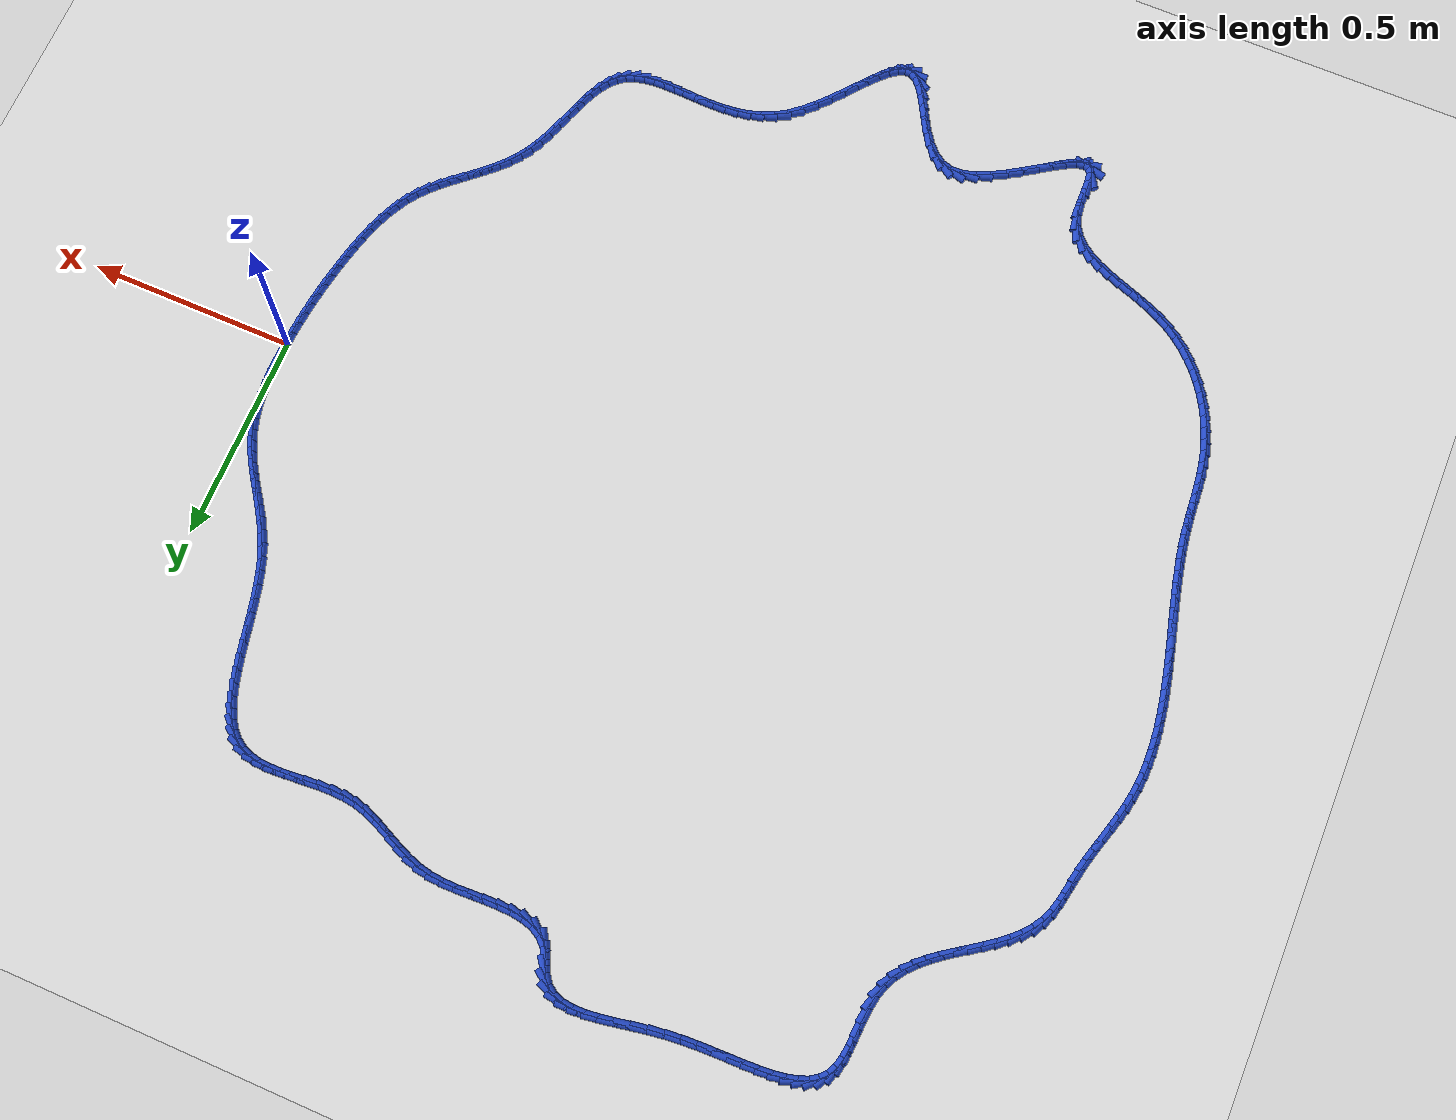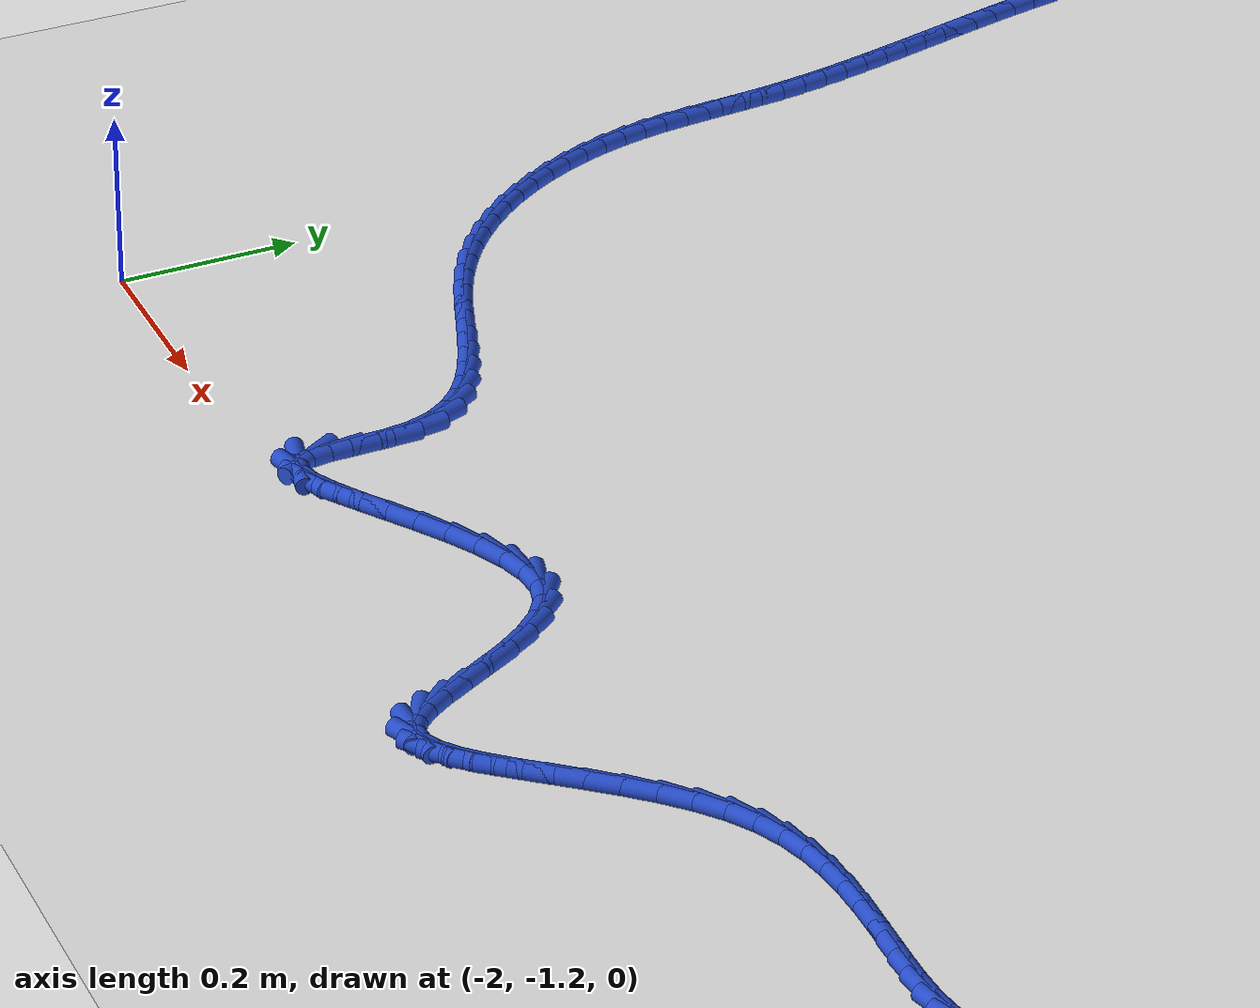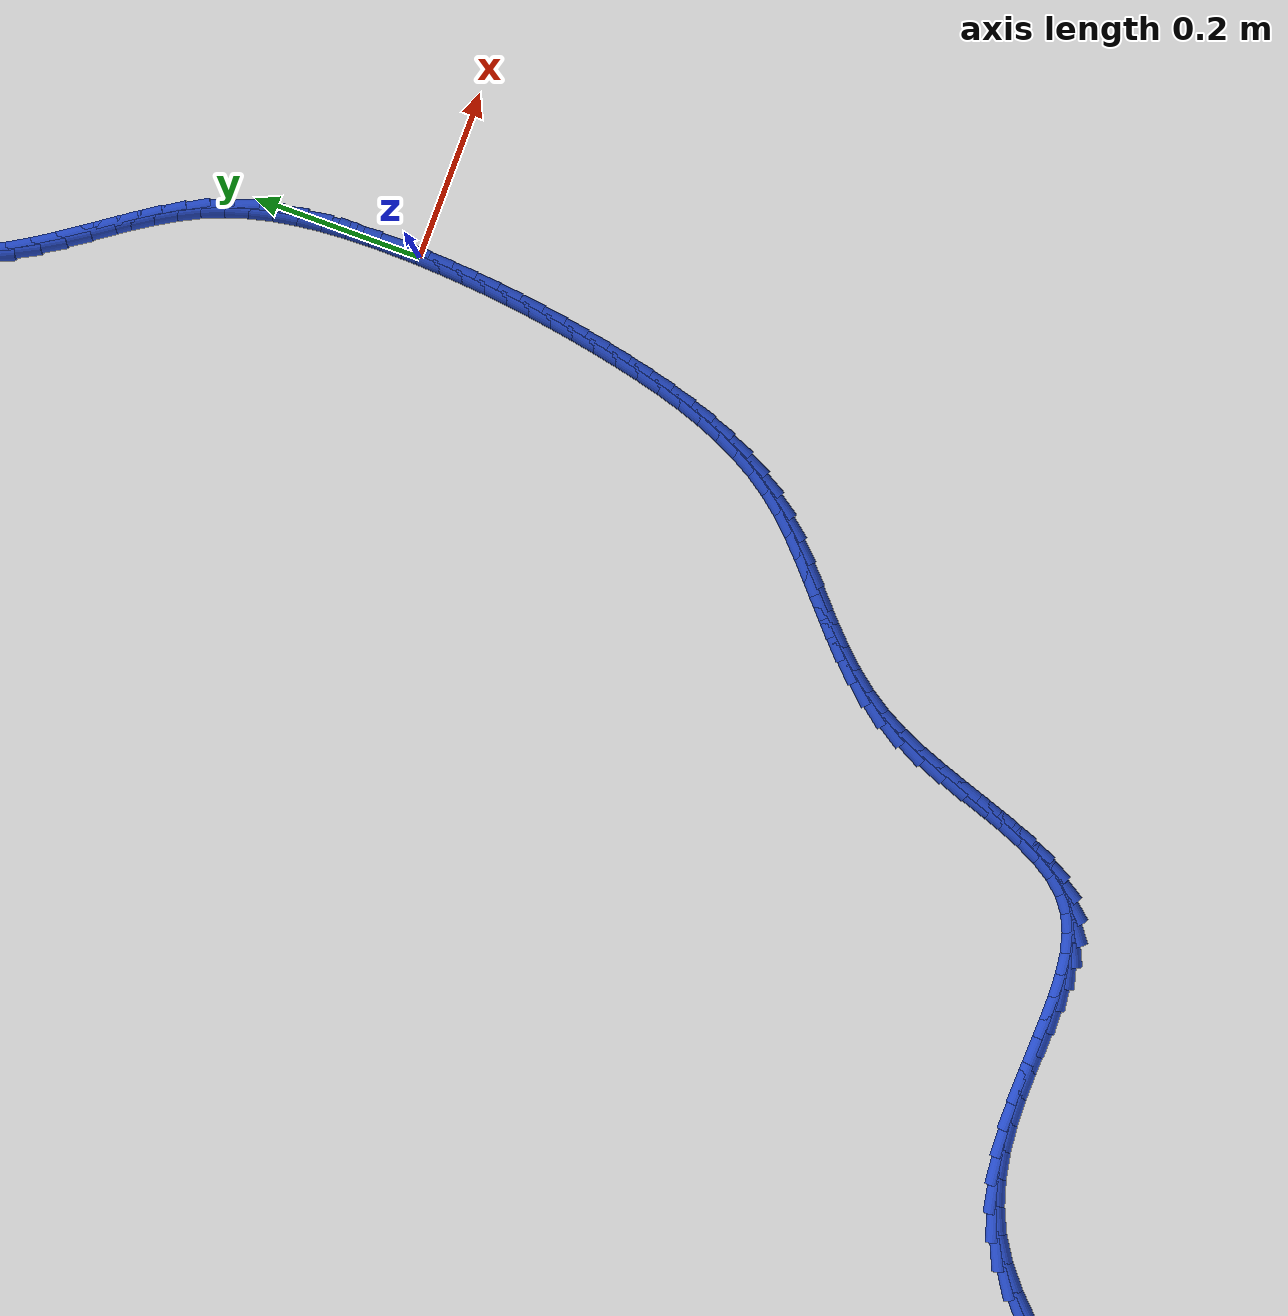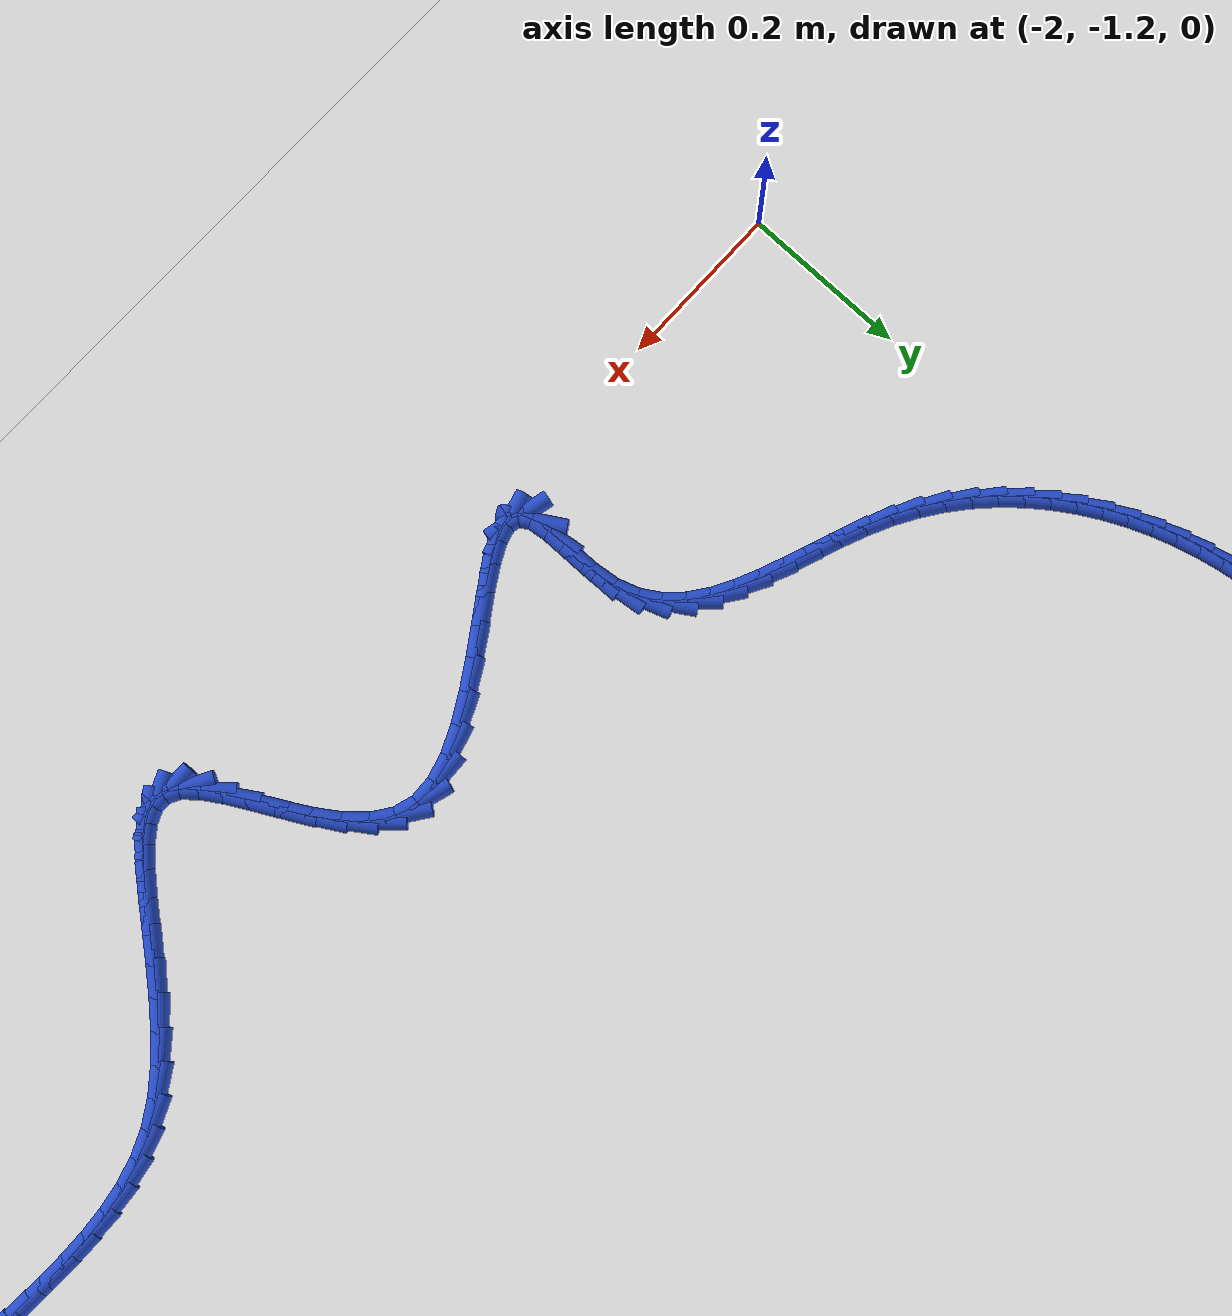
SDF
<sdf version="1.6">
 <world name="default">
  <light name="sun" type="directional">
   <pose>0 0 10 0 -0 0</pose>
   <diffuse>0.8 0.8 0.8 1</diffuse>
   <specular>0.2 0.2 0.2 1</specular>
   <attenuation>
    <range>1000</range>
    <constant>0.9</constant>
    <linear>0.01</linear>
    <quadratic>0.001</quadratic>
   </attenuation>
   <direction>-0.5 0.1 -0.9</direction>
  </light>
  <model name="ground_plane">
   <static>1</static>
   <link name="link">
    <collision name="collision">
     <geometry><plane><normal>0 0 1</normal><size>100 100</size></plane></geometry>
     <surface><friction><ode><mu>100</mu><mu2>50</mu2></ode></friction></surface>
    </collision>
    <visual name="visual">
     <cast_shadows>0</cast_shadows>
     <geometry><plane><normal>0 0 1</normal><size>100 100</size></plane></geometry>
     <material>
      <script><uri>file://media/materials/scripts/gazebo.material</uri><name>Gazebo/WhiteGlow</name></script>
     </material>
    </visual>
   </link>
  </model>
  <gravity>0 0 -9.8</gravity>
  <magnetic_field>6e-06 2.3e-05 -4.2e-05</magnetic_field>
  <atmosphere type="adiabatic"/>
  <physics name="default_physics" default="0" type="ode">
   <max_step_size>0.001</max_step_size>
   <real_time_factor>1</real_time_factor>
   <real_time_update_rate>1000</real_time_update_rate>
  </physics>
  <scene><ambient>0.4 0.4 0.4 1</ambient><background>0.7 0.7 0.7 1</background><shadows>1</shadows></scene>
  <spherical_coordinates>
   <surface_model>EARTH_WGS84</surface_model>
   <latitude_deg>0</latitude_deg>
   <longitude_deg>0</longitude_deg>
   <elevation>0</elevation>
   <heading_deg>0</heading_deg>
  </spherical_coordinates>
  <model name="line">
   <link name="link_0">
    <pose>-6.396792817664476e-18 4.163336342344337e-17 0.01 0 1.57 1.54245428637409</pose>
    <collision name="collision">
     <geometry><cylinder><radius>0.01</radius><length>0.08</length></cylinder></geometry>
    </collision>
    <visual name="visual">
     <material>
      <script><name>Gazebo/Blue</name><uri>file://media/materials/scripts/gazebo.material</uri></script>
     </material>
     <geometry><cylinder><radius>0.01</radius><length>0.08</length></cylinder></geometry>
    </visual>
   </link>
   <link name="link_1">
    <pose>0.0008248467116915636 0.029095500149906025 0.01 0 1.57 1.5677693399325823</pose>
    <collision name="collision">
     <geometry><cylinder><radius>0.01</radius><length>0.08</length></cylinder></geometry>
    </collision>
    <visual name="visual">
     <material>
      <script><name>Gazebo/Blue</name><uri>file://media/materials/scripts/gazebo.material</uri></script>
     </material>
     <geometry><cylinder><radius>0.01</radius><length>0.08</length></cylinder></geometry>
    </visual>
   </link>
   <link name="link_2">
    <pose>0.0009134119182850745 0.05835394761747079 0.01 0 1.57 -1.5422264359774394</pose>
    <collision name="collision">
     <geometry><cylinder><radius>0.01</radius><length>0.08</length></cylinder></geometry>
    </collision>
    <visual name="visual">
     <material>
      <script><name>Gazebo/Blue</name><uri>file://media/materials/scripts/gazebo.material</uri></script>
     </material>
     <geometry><cylinder><radius>0.01</radius><length>0.08</length></cylinder></geometry>
    </visual>
   </link>
   <link name="link_3">
    <pose>7.768115417044726e-05 0.08759813940753491 0.01 0 1.57 -1.5038446356973172</pose>
    <collision name="collision">
     <geometry><cylinder><radius>0.01</radius><length>0.08</length></cylinder></geometry>
    </collision>
    <visual name="visual">
     <material>
      <script><name>Gazebo/Blue</name><uri>file://media/materials/scripts/gazebo.material</uri></script>
     </material>
     <geometry><cylinder><radius>0.01</radius><length>0.08</length></cylinder></geometry>
    </visual>
   </link>
   <link name="link_4">
    <pose>-0.0018703600462624012 0.11665087252493883 0.01 0 1.57 -1.4580304136091649</pose>
    <collision name="collision">
     <geometry><cylinder><radius>0.01</radius><length>0.08</length></cylinder></geometry>
    </collision>
    <visual name="visual">
     <material>
      <script><name>Gazebo/Blue</name><uri>file://media/materials/scripts/gazebo.material</uri></script>
     </material>
     <geometry><cylinder><radius>0.01</radius><length>0.08</length></cylinder></geometry>
    </visual>
   </link>
   <link name="link_5">
    <pose>-0.005118726148623548 0.14533494397452312 0.01 0 1.57 -1.4040227581456983</pose>
    <collision name="collision">
     <geometry><cylinder><radius>0.01</radius><length>0.08</length></cylinder></geometry>
    </collision>
    <visual name="visual">
     <material>
      <script><name>Gazebo/Blue</name><uri>file://media/materials/scripts/gazebo.material</uri></script>
     </material>
     <geometry><cylinder><radius>0.01</radius><length>0.08</length></cylinder></geometry>
    </visual>
   </link>
   <link name="link_6">
    <pose>-0.009855431618523081 0.17347315076112838 0.01 0 1.57 -1.341004287895014</pose>
    <collision name="collision">
     <geometry><cylinder><radius>0.01</radius><length>0.08</length></cylinder></geometry>
    </collision>
    <visual name="visual">
     <material>
      <script><name>Gazebo/Blue</name><uri>file://media/materials/scripts/gazebo.material</uri></script>
     </material>
     <geometry><cylinder><radius>0.01</radius><length>0.08</length></cylinder></geometry>
    </visual>
   </link>
   <link name="link_7">
    <pose>-0.016268490921571073 0.20088828988959495 0.01 0 1.57 -1.268202466706276</pose>
    <collision name="collision">
     <geometry><cylinder><radius>0.01</radius><length>0.08</length></cylinder></geometry>
    </collision>
    <visual name="visual">
     <material>
      <script><name>Gazebo/Blue</name><uri>file://media/materials/scripts/gazebo.material</uri></script>
     </material>
     <geometry><cylinder><radius>0.01</radius><length>0.08</length></cylinder></geometry>
    </visual>
   </link>
   <link name="link_8">
    <pose>-0.024545918523377612 0.22740315836476355 0.01 0 1.57 -1.1857203393625144</pose>
    <collision name="collision">
     <geometry><cylinder><radius>0.01</radius><length>0.08</length></cylinder></geometry>
    </collision>
    <visual name="visual">
     <material>
      <script><name>Gazebo/Blue</name><uri>file://media/materials/scripts/gazebo.material</uri></script>
     </material>
     <geometry><cylinder><radius>0.01</radius><length>0.08</length></cylinder></geometry>
    </visual>
   </link>
   <link name="link_9">
    <pose>-0.034860855251699574 0.25285262720387897 0.01 0 1.57 -1.1068173142942233</pose>
    <collision name="collision">
     <geometry><cylinder><radius>0.01</radius><length>0.08</length></cylinder></geometry>
    </collision>
    <visual name="visual">
     <material>
      <script><name>Gazebo/Blue</name><uri>file://media/materials/scripts/gazebo.material</uri></script>
     </material>
     <geometry><cylinder><radius>0.01</radius><length>0.08</length></cylinder></geometry>
    </visual>
   </link>
   <link name="link_10">
    <pose>-0.047097666821547056 0.27730598716250304 0.01 0 1.57 -1.0448218522410508</pose>
    <collision name="collision">
     <geometry><cylinder><radius>0.01</radius><length>0.08</length></cylinder></geometry>
    </collision>
    <visual name="visual">
     <material>
      <script><name>Gazebo/Blue</name><uri>file://media/materials/scripts/gazebo.material</uri></script>
     </material>
     <geometry><cylinder><radius>0.01</radius><length>0.08</length></cylinder></geometry>
    </visual>
   </link>
   <link name="link_11">
    <pose>-0.060878784411462404 0.3010451602888011 0.01 0 1.57 -1.0009656076182503</pose>
    <collision name="collision">
     <geometry><cylinder><radius>0.01</radius><length>0.08</length></cylinder></geometry>
    </collision>
    <visual name="visual">
     <material>
      <script><name>Gazebo/Blue</name><uri>file://media/materials/scripts/gazebo.material</uri></script>
     </material>
     <geometry><cylinder><radius>0.01</radius><length>0.08</length></cylinder></geometry>
    </visual>
   </link>
   <link name="link_12">
    <pose>-0.07581714969714255 0.3243597719498032 0.01 0 1.57 -0.9752033165678898</pose>
    <collision name="collision">
     <geometry><cylinder><radius>0.01</radius><length>0.08</length></cylinder></geometry>
    </collision>
    <visual name="visual">
     <material>
      <script><name>Gazebo/Blue</name><uri>file://media/materials/scripts/gazebo.material</uri></script>
     </material>
     <geometry><cylinder><radius>0.01</radius><length>0.08</length></cylinder></geometry>
    </visual>
   </link>
   <link name="link_13">
    <pose>-0.09152570435428442 0.34753944751253957 0.01 0 1.57 -0.9670754464203306</pose>
    <collision name="collision">
     <geometry><cylinder><radius>0.01</radius><length>0.08</length></cylinder></geometry>
    </collision>
    <visual name="visual">
     <material>
      <script><name>Gazebo/Blue</name><uri>file://media/materials/scripts/gazebo.material</uri></script>
     </material>
     <geometry><cylinder><radius>0.01</radius><length>0.08</length></cylinder></geometry>
    </visual>
   </link>
   <link name="link_14">
    <pose>-0.10761739005858495 0.3708738123440406 0.01 0 1.57 -0.9759741425558733</pose>
    <collision name="collision">
     <geometry><cylinder><radius>0.01</radius><length>0.08</length></cylinder></geometry>
    </collision>
    <visual name="visual">
     <material>
      <script><name>Gazebo/Blue</name><uri>file://media/materials/scripts/gazebo.material</uri></script>
     </material>
     <geometry><cylinder><radius>0.01</radius><length>0.08</length></cylinder></geometry>
    </visual>
   </link>
   <link name="link_15">
    <pose>-0.12370514848574109 0.39465249181133627 0.01 0 1.57 -1.0012314942445295</pose>
    <collision name="collision">
     <geometry><cylinder><radius>0.01</radius><length>0.08</length></cylinder></geometry>
    </collision>
    <visual name="visual">
     <material>
      <script><name>Gazebo/Blue</name><uri>file://media/materials/scripts/gazebo.material</uri></script>
     </material>
     <geometry><cylinder><radius>0.01</radius><length>0.08</length></cylinder></geometry>
    </visual>
   </link>
   <link name="link_16">
    <pose>-0.13940192131144968 0.41916511128145656 0.01 0 1.57 -1.0420611925751466</pose>
    <collision name="collision">
     <geometry><cylinder><radius>0.01</radius><length>0.08</length></cylinder></geometry>
    </collision>
    <visual name="visual">
     <material>
      <script><name>Gazebo/Blue</name><uri>file://media/materials/scripts/gazebo.material</uri></script>
     </material>
     <geometry><cylinder><radius>0.01</radius><length>0.08</length></cylinder></geometry>
    </visual>
   </link>
   <link name="link_17">
    <pose>-0.15432065021140776 0.44470129612143205 0.01 0 1.57 -1.0973958093674703</pose>
    <collision name="collision">
     <geometry><cylinder><radius>0.01</radius><length>0.08</length></cylinder></geometry>
    </collision>
    <visual name="visual">
     <material>
      <script><name>Gazebo/Blue</name><uri>file://media/materials/scripts/gazebo.material</uri></script>
     </material>
     <geometry><cylinder><radius>0.01</radius><length>0.08</length></cylinder></geometry>
    </visual>
   </link>
   <link name="link_18">
    <pose>-0.16807427686131227 0.471550671698293 0.01 0 1.57 -1.1650815043284315</pose>
    <collision name="collision">
     <geometry><cylinder><radius>0.01</radius><length>0.08</length></cylinder></geometry>
    </collision>
    <visual name="visual">
     <material>
      <script><name>Gazebo/Blue</name><uri>file://media/materials/scripts/gazebo.material</uri></script>
     </material>
     <geometry><cylinder><radius>0.01</radius><length>0.08</length></cylinder></geometry>
    </visual>
   </link>
   <link name="link_19">
    <pose>-0.18028986768407876 0.499989049497895 0.01 0 1.57 -1.2301213299915739</pose>
    <collision name="collision">
     <geometry><cylinder><radius>0.01</radius><length>0.08</length></cylinder></geometry>
    </collision>
    <visual name="visual">
     <material>
      <script><name>Gazebo/Blue</name><uri>file://media/materials/scripts/gazebo.material</uri></script>
     </material>
     <geometry><cylinder><radius>0.01</radius><length>0.08</length></cylinder></geometry>
    </visual>
   </link>
   <link name="link_20">
    <pose>-0.19091954757558063 0.5299743366181011 0.01 0 1.57 -1.2802395257758827</pose>
    <collision name="collision">
     <geometry><cylinder><radius>0.01</radius><length>0.08</length></cylinder></geometry>
    </collision>
    <visual name="visual">
     <material>
      <script><name>Gazebo/Blue</name><uri>file://media/materials/scripts/gazebo.material</uri></script>
     </material>
     <geometry><cylinder><radius>0.01</radius><length>0.08</length></cylinder></geometry>
    </visual>
   </link>
   <link name="link_21">
    <pose>-0.20024060509884234 0.5611464328897653 0.01 0 1.57 -1.3167862494645184</pose>
    <collision name="collision">
     <geometry><cylinder><radius>0.01</radius><length>0.08</length></cylinder></geometry>
    </collision>
    <visual name="visual">
     <material>
      <script><name>Gazebo/Blue</name><uri>file://media/materials/scripts/gazebo.material</uri></script>
     </material>
     <geometry><cylinder><radius>0.01</radius><length>0.08</length></cylinder></geometry>
    </visual>
   </link>
   <link name="link_22">
    <pose>-0.20854447460294634 0.5931314036867638 0.01 0 1.57 -1.3411977398994734</pose>
    <collision name="collision">
     <geometry><cylinder><radius>0.01</radius><length>0.08</length></cylinder></geometry>
    </collision>
    <visual name="visual">
     <material>
      <script><name>Gazebo/Blue</name><uri>file://media/materials/scripts/gazebo.material</uri></script>
     </material>
     <geometry><cylinder><radius>0.01</radius><length>0.08</length></cylinder></geometry>
    </visual>
   </link>
   <link name="link_23">
    <pose>-0.21612259043697518 0.6255553143829725 0.01 0 1.57 -1.3543565602587473</pose>
    <collision name="collision">
     <geometry><cylinder><radius>0.01</radius><length>0.08</length></cylinder></geometry>
    </collision>
    <visual name="visual">
     <material>
      <script><name>Gazebo/Blue</name><uri>file://media/materials/scripts/gazebo.material</uri></script>
     </material>
     <geometry><cylinder><radius>0.01</radius><length>0.08</length></cylinder></geometry>
    </visual>
   </link>
   <link name="link_24">
    <pose>-0.2232663869500115 0.6580442303522681 0.01 0 1.57 -1.356579501501783</pose>
    <collision name="collision">
     <geometry><cylinder><radius>0.01</radius><length>0.08</length></cylinder></geometry>
    </collision>
    <visual name="visual">
     <material>
      <script><name>Gazebo/Blue</name><uri>file://media/materials/scripts/gazebo.material</uri></script>
     </material>
     <geometry><cylinder><radius>0.01</radius><length>0.08</length></cylinder></geometry>
    </visual>
   </link>
   <link name="link_25">
    <pose>-0.2302672984911376 0.6902242169685261 0.01 0 1.57 -1.3475907251236856</pose>
    <collision name="collision">
     <geometry><cylinder><radius>0.01</radius><length>0.08</length></cylinder></geometry>
    </collision>
    <visual name="visual">
     <material>
      <script><name>Gazebo/Blue</name><uri>file://media/materials/scripts/gazebo.material</uri></script>
     </material>
     <geometry><cylinder><radius>0.01</radius><length>0.08</length></cylinder></geometry>
    </visual>
   </link>
   <link name="link_26">
    <pose>-0.23741675940943613 0.721721339605623 0.01 0 1.57 -1.3264558157334978</pose>
    <collision name="collision">
     <geometry><cylinder><radius>0.01</radius><length>0.08</length></cylinder></geometry>
    </collision>
    <visual name="visual">
     <material>
      <script><name>Gazebo/Blue</name><uri>file://media/materials/scripts/gazebo.material</uri></script>
     </material>
     <geometry><cylinder><radius>0.01</radius><length>0.08</length></cylinder></geometry>
    </visual>
   </link>
   <link name="link_27">
    <pose>-0.24500620405398954 0.7521616636374349 0.01 0 1.57 -1.2914641315655584</pose>
    <collision name="collision">
     <geometry><cylinder><radius>0.01</radius><length>0.08</length></cylinder></geometry>
    </collision>
    <visual name="visual">
     <material>
      <script><name>Gazebo/Blue</name><uri>file://media/materials/scripts/gazebo.material</uri></script>
     </material>
     <geometry><cylinder><radius>0.01</radius><length>0.08</length></cylinder></geometry>
    </visual>
   </link>
   <link name="link_28">
    <pose>-0.25332706677388034 0.7811712544378376 0.01 0 1.57 -1.2399625101100733</pose>
    <collision name="collision">
     <geometry><cylinder><radius>0.01</radius><length>0.08</length></cylinder></geometry>
    </collision>
    <visual name="visual">
     <material>
      <script><name>Gazebo/Blue</name><uri>file://media/materials/scripts/gazebo.material</uri></script>
     </material>
     <geometry><cylinder><radius>0.01</radius><length>0.08</length></cylinder></geometry>
    </visual>
   </link>
   <link name="link_29">
    <pose>-0.262670781918191 0.8083761773807077 0.01 0 1.57 -1.168187563916338</pose>
    <collision name="collision">
     <geometry><cylinder><radius>0.01</radius><length>0.08</length></cylinder></geometry>
    </collision>
    <visual name="visual">
     <material>
      <script><name>Gazebo/Blue</name><uri>file://media/materials/scripts/gazebo.material</uri></script>
     </material>
     <geometry><cylinder><radius>0.01</radius><length>0.08</length></cylinder></geometry>
    </visual>
   </link>
   <link name="link_30">
    <pose>-0.2733287838360041 0.8334024978399209 0.01 0 1.57 -1.0712680139525315</pose>
    <collision name="collision">
     <geometry><cylinder><radius>0.01</radius><length>0.08</length></cylinder></geometry>
    </collision>
    <visual name="visual">
     <material>
      <script><name>Gazebo/Blue</name><uri>file://media/materials/scripts/gazebo.material</uri></script>
     </material>
     <geometry><cylinder><radius>0.01</radius><length>0.08</length></cylinder></geometry>
    </visual>
   </link>
   <link name="link_31">
    <pose>-0.28559250687640225 0.8558762811893538 0.01 0 1.57 -0.943854486773389</pose>
    <collision name="collision">
     <geometry><cylinder><radius>0.01</radius><length>0.08</length></cylinder></geometry>
    </collision>
    <visual name="visual">
     <material>
      <script><name>Gazebo/Blue</name><uri>file://media/materials/scripts/gazebo.material</uri></script>
     </material>
     <geometry><cylinder><radius>0.01</radius><length>0.08</length></cylinder></geometry>
    </visual>
   </link>
   <link name="link_32">
    <pose>-0.29975338538846774 0.8754235928028822 0.01 0 1.57 -0.782251716981026</pose>
    <collision name="collision">
     <geometry><cylinder><radius>0.01</radius><length>0.08</length></cylinder></geometry>
    </collision>
    <visual name="visual">
     <material>
      <script><name>Gazebo/Blue</name><uri>file://media/materials/scripts/gazebo.material</uri></script>
     </material>
     <geometry><cylinder><radius>0.01</radius><length>0.08</length></cylinder></geometry>
    </visual>
   </link>
   <link name="link_33">
    <pose>-0.3161028537212831 0.8916704980543821 0.01 0 1.57 -0.5887217653913093</pose>
    <collision name="collision">
     <geometry><cylinder><radius>0.01</radius><length>0.08</length></cylinder></geometry>
    </collision>
    <visual name="visual">
     <material>
      <script><name>Gazebo/Blue</name><uri>file://media/materials/scripts/gazebo.material</uri></script>
     </material>
     <geometry><cylinder><radius>0.01</radius><length>0.08</length></cylinder></geometry>
    </visual>
   </link>
   <link name="link_34">
    <pose>-0.3349323462239311 0.9042430623177302 0.01 0 1.57 -0.3766655392250517</pose>
    <collision name="collision">
     <geometry><cylinder><radius>0.01</radius><length>0.08</length></cylinder></geometry>
    </collision>
    <visual name="visual">
     <material>
      <script><name>Gazebo/Blue</name><uri>file://media/materials/scripts/gazebo.material</uri></script>
     </material>
     <geometry><cylinder><radius>0.01</radius><length>0.08</length></cylinder></geometry>
    </visual>
   </link>
   <link name="link_35">
    <pose>-0.35652312889490695 0.9127833275080758 0.01 0 1.57 -0.19021077041386</pose>
    <collision name="collision">
     <geometry><cylinder><radius>0.01</radius><length>0.08</length></cylinder></geometry>
    </collision>
    <visual name="visual">
     <material>
      <script><name>Gazebo/Blue</name><uri>file://media/materials/scripts/gazebo.material</uri></script>
     </material>
     <geometry><cylinder><radius>0.01</radius><length>0.08</length></cylinder></geometry>
    </visual>
   </link>
   <link name="link_36">
    <pose>-0.38082033230206713 0.9174614724822471 0.01 0 1.57 -0.06106410085704112</pose>
    <collision name="collision">
     <geometry><cylinder><radius>0.01</radius><length>0.08</length></cylinder></geometry>
    </collision>
    <visual name="visual">
     <material>
      <script><name>Gazebo/Blue</name><uri>file://media/materials/scripts/gazebo.material</uri></script>
     </material>
     <geometry><cylinder><radius>0.01</radius><length>0.08</length></cylinder></geometry>
    </visual>
   </link>
   <link name="link_37">
    <pose>-0.4073638741852602 0.9190843476413585 0.01 0 1.57 0.020756921790680685</pose>
    <collision name="collision">
     <geometry><cylinder><radius>0.01</radius><length>0.08</length></cylinder></geometry>
    </collision>
    <visual name="visual">
     <material>
      <script><name>Gazebo/Blue</name><uri>file://media/materials/scripts/gazebo.material</uri></script>
     </material>
     <geometry><cylinder><radius>0.01</radius><length>0.08</length></cylinder></geometry>
    </visual>
   </link>
   <link name="link_38">
    <pose>-0.4356695369977032 0.9184967248173106 0.01 0 1.57 0.0659324734508826</pose>
    <collision name="collision">
     <geometry><cylinder><radius>0.01</radius><length>0.08</length></cylinder></geometry>
    </collision>
    <visual name="visual">
     <material>
      <script><name>Gazebo/Blue</name><uri>file://media/materials/scripts/gazebo.material</uri></script>
     </material>
     <geometry><cylinder><radius>0.01</radius><length>0.08</length></cylinder></geometry>
    </visual>
   </link>
   <link name="link_39">
    <pose>-0.465253103192613 0.9165433758420046 0.01 0 1.57 0.08127308688358488</pose>
    <collision name="collision">
     <geometry><cylinder><radius>0.01</radius><length>0.08</length></cylinder></geometry>
    </collision>
    <visual name="visual">
     <material>
      <script><name>Gazebo/Blue</name><uri>file://media/materials/scripts/gazebo.material</uri></script>
     </material>
     <geometry><cylinder><radius>0.01</radius><length>0.08</length></cylinder></geometry>
    </visual>
   </link>
   <link name="link_40">
    <pose>-0.49563035522320587 0.9140690725473415 0.01 0 1.57 0.06996432766600989</pose>
    <collision name="collision">
     <geometry><cylinder><radius>0.01</radius><length>0.08</length></cylinder></geometry>
    </collision>
    <visual name="visual">
     <material>
      <script><name>Gazebo/Blue</name><uri>file://media/materials/scripts/gazebo.material</uri></script>
     </material>
     <geometry><cylinder><radius>0.01</radius><length>0.08</length></cylinder></geometry>
    </visual>
   </link>
   <link name="link_41">
    <pose>-0.5263170755426992 0.9119185867652225 0.01 0 1.57 0.03216959325350356</pose>
    <collision name="collision">
     <geometry><cylinder><radius>0.01</radius><length>0.08</length></cylinder></geometry>
    </collision>
    <visual name="visual">
     <material>
      <script><name>Gazebo/Blue</name><uri>file://media/materials/scripts/gazebo.material</uri></script>
     </material>
     <geometry><cylinder><radius>0.01</radius><length>0.08</length></cylinder></geometry>
    </visual>
   </link>
   <link name="link_42">
    <pose>-0.5568290466043099 0.9109366903275481 0.01 0 1.57 -0.03453771581233891</pose>
    <collision name="collision">
     <geometry><cylinder><radius>0.01</radius><length>0.08</length></cylinder></geometry>
    </collision>
    <visual name="visual">
     <material>
      <script><name>Gazebo/Blue</name><uri>file://media/materials/scripts/gazebo.material</uri></script>
     </material>
     <geometry><cylinder><radius>0.01</radius><length>0.08</length></cylinder></geometry>
    </visual>
   </link>
   <link name="link_43">
    <pose>-0.5866820508612548 0.91196815506622 0.01 0 1.57 -0.13461835076470766</pose>
    <collision name="collision">
     <geometry><cylinder><radius>0.01</radius><length>0.08</length></cylinder></geometry>
    </collision>
    <visual name="visual">
     <material>
      <script><name>Gazebo/Blue</name><uri>file://media/materials/scripts/gazebo.material</uri></script>
     </material>
     <geometry><cylinder><radius>0.01</radius><length>0.08</length></cylinder></geometry>
    </visual>
   </link>
   <link name="link_44">
    <pose>-0.6153924740073257 0.9158566223719713 0.01 0 1.57 -0.2557452301849412</pose>
    <collision name="collision">
     <geometry><cylinder><radius>0.01</radius><length>0.08</length></cylinder></geometry>
    </collision>
    <visual name="visual">
     <material>
      <script><name>Gazebo/Blue</name><uri>file://media/materials/scripts/gazebo.material</uri></script>
     </material>
     <geometry><cylinder><radius>0.01</radius><length>0.08</length></cylinder></geometry>
    </visual>
   </link>
   <link name="link_45">
    <pose>-0.6427143023420219 0.9230004825749244 0.01 0 1.57 -0.3527483318246726</pose>
    <collision name="collision">
     <geometry><cylinder><radius>0.01</radius><length>0.08</length></cylinder></geometry>
    </collision>
    <visual name="visual">
     <material>
      <script><name>Gazebo/Blue</name><uri>file://media/materials/scripts/gazebo.material</uri></script>
     </material>
     <geometry><cylinder><radius>0.01</radius><length>0.08</length></cylinder></geometry>
    </visual>
   </link>
   <link name="link_46">
    <pose>-0.668999620255764 0.9326773215840979 0.01 0 1.57 -0.41478934054829303</pose>
    <collision name="collision">
     <geometry><cylinder><radius>0.01</radius><length>0.08</length></cylinder></geometry>
    </collision>
    <visual name="visual">
     <material>
      <script><name>Gazebo/Blue</name><uri>file://media/materials/scripts/gazebo.material</uri></script>
     </material>
     <geometry><cylinder><radius>0.01</radius><length>0.08</length></cylinder></geometry>
    </visual>
   </link>
   <link name="link_47">
    <pose>-0.6946931450149568 0.9439911361623159 0.01 0 1.57 -0.44089733472905185</pose>
    <collision name="collision">
     <geometry><cylinder><radius>0.01</radius><length>0.08</length></cylinder></geometry>
    </collision>
    <visual name="visual">
     <material>
      <script><name>Gazebo/Blue</name><uri>file://media/materials/scripts/gazebo.material</uri></script>
     </material>
     <geometry><cylinder><radius>0.01</radius><length>0.08</length></cylinder></geometry>
    </visual>
   </link>
   <link name="link_48">
    <pose>-0.720239593886006 0.9560459230724025 0.01 0 1.57 -0.4315051273858564</pose>
    <collision name="collision">
     <geometry><cylinder><radius>0.01</radius><length>0.08</length></cylinder></geometry>
    </collision>
    <visual name="visual">
     <material>
      <script><name>Gazebo/Blue</name><uri>file://media/materials/scripts/gazebo.material</uri></script>
     </material>
     <geometry><cylinder><radius>0.01</radius><length>0.08</length></cylinder></geometry>
    </visual>
   </link>
   <link name="link_49">
    <pose>-0.7460836841353166 0.967945679077182 0.01 0 1.57 -0.3874306257747195</pose>
    <collision name="collision">
     <geometry><cylinder><radius>0.01</radius><length>0.08</length></cylinder></geometry>
    </collision>
    <visual name="visual">
     <material>
      <script><name>Gazebo/Blue</name><uri>file://media/materials/scripts/gazebo.material</uri></script>
     </material>
     <geometry><cylinder><radius>0.01</radius><length>0.08</length></cylinder></geometry>
    </visual>
   </link>
   <link name="link_50">
    <pose>-0.7726701330292942 0.9787944009394788 0.01 0 1.57 -0.3101652433635925</pose>
    <collision name="collision">
     <geometry><cylinder><radius>0.01</radius><length>0.08</length></cylinder></geometry>
    </collision>
    <visual name="visual">
     <material>
      <script><name>Gazebo/Blue</name><uri>file://media/materials/scripts/gazebo.material</uri></script>
     </material>
     <geometry><cylinder><radius>0.01</radius><length>0.08</length></cylinder></geometry>
    </visual>
   </link>
   <link name="link_51">
    <pose>-0.8004436578343439 0.987696085422117 0.01 0 1.57 -0.20323898843638474</pose>
    <collision name="collision">
     <geometry><cylinder><radius>0.01</radius><length>0.08</length></cylinder></geometry>
    </collision>
    <visual name="visual">
     <material>
      <script><name>Gazebo/Blue</name><uri>file://media/materials/scripts/gazebo.material</uri></script>
     </material>
     <geometry><cylinder><radius>0.01</radius><length>0.08</length></cylinder></geometry>
    </visual>
   </link>
   <link name="link_52">
    <pose>-0.8298482817374023 0.9937559180988316 0.01 0 1.57 -0.08980574394000662</pose>
    <collision name="collision">
     <geometry><cylinder><radius>0.01</radius><length>0.08</length></cylinder></geometry>
    </collision>
    <visual name="visual">
     <material>
      <script><name>Gazebo/Blue</name><uri>file://media/materials/scripts/gazebo.material</uri></script>
     </material>
     <geometry><cylinder><radius>0.01</radius><length>0.08</length></cylinder></geometry>
    </visual>
   </link>
   <link name="link_53">
    <pose>-0.8610442969728522 0.9965650554833674 0.01 0 1.57 -0.011738203919469652</pose>
    <collision name="collision">
     <geometry><cylinder><radius>0.01</radius><length>0.08</length></cylinder></geometry>
    </collision>
    <visual name="visual">
     <material>
      <script><name>Gazebo/Blue</name><uri>file://media/materials/scripts/gazebo.material</uri></script>
     </material>
     <geometry><cylinder><radius>0.01</radius><length>0.08</length></cylinder></geometry>
    </visual>
   </link>
   <link name="link_54">
    <pose>-0.8934732398634755 0.9969457305118953 0.01 0 1.57 0.03131801979265752</pose>
    <collision name="collision">
     <geometry><cylinder><radius>0.01</radius><length>0.08</length></cylinder></geometry>
    </collision>
    <visual name="visual">
     <material>
      <script><name>Gazebo/Blue</name><uri>file://media/materials/scripts/gazebo.material</uri></script>
     </material>
     <geometry><cylinder><radius>0.01</radius><length>0.08</length></cylinder></geometry>
    </visual>
   </link>
   <link name="link_55">
    <pose>-0.9264645523620343 0.9959121700002723 0.01 0 1.57 0.04356830733985392</pose>
    <collision name="collision">
     <geometry><cylinder><radius>0.01</radius><length>0.08</length></cylinder></geometry>
    </collision>
    <visual name="visual">
     <material>
      <script><name>Gazebo/Blue</name><uri>file://media/materials/scripts/gazebo.material</uri></script>
     </material>
     <geometry><cylinder><radius>0.01</radius><length>0.08</length></cylinder></geometry>
    </visual>
   </link>
   <link name="link_56">
    <pose>-0.9593476764212902 0.9944786007643565 0.01 0 1.57 0.025515938390088155</pose>
    <collision name="collision">
     <geometry><cylinder><radius>0.01</radius><length>0.08</length></cylinder></geometry>
    </collision>
    <visual name="visual">
     <material>
      <script><name>Gazebo/Blue</name><uri>file://media/materials/scripts/gazebo.material</uri></script>
     </material>
     <geometry><cylinder><radius>0.01</radius><length>0.08</length></cylinder></geometry>
    </visual>
   </link>
   <link name="link_57">
    <pose>-0.9914520539940062 0.9936592496200052 0.01 0 1.57 -0.026387344268824643</pose>
    <collision name="collision">
     <geometry><cylinder><radius>0.01</radius><length>0.08</length></cylinder></geometry>
    </collision>
    <visual name="visual">
     <material>
      <script><name>Gazebo/Blue</name><uri>file://media/materials/scripts/gazebo.material</uri></script>
     </material>
     <geometry><cylinder><radius>0.01</radius><length>0.08</length></cylinder></geometry>
    </visual>
   </link>
   <link name="link_58">
    <pose>-1.0221071270329445 0.9944683433830752 0.01 0 1.57 -0.12038024804437959</pose>
    <collision name="collision">
     <geometry><cylinder><radius>0.01</radius><length>0.08</length></cylinder></geometry>
    </collision>
    <visual name="visual">
     <material>
      <script><name>Gazebo/Blue</name><uri>file://media/materials/scripts/gazebo.material</uri></script>
     </material>
     <geometry><cylinder><radius>0.01</radius><length>0.08</length></cylinder></geometry>
    </visual>
   </link>
   <link name="link_59">
    <pose>-1.0506423374908676 0.9979201088694247 0.01 0 1.57 -0.2694076243725932</pose>
    <collision name="collision">
     <geometry><cylinder><radius>0.01</radius><length>0.08</length></cylinder></geometry>
    </collision>
    <visual name="visual">
     <material>
      <script><name>Gazebo/Blue</name><uri>file://media/materials/scripts/gazebo.material</uri></script>
     </material>
     <geometry><cylinder><radius>0.01</radius><length>0.08</length></cylinder></geometry>
    </visual>
   </link>
   <link name="link_60">
    <pose>-1.0763871273205372 1.0050287728949108 0.01 0 1.57 -0.48628484540770645</pose>
    <collision name="collision">
     <geometry><cylinder><radius>0.01</radius><length>0.08</length></cylinder></geometry>
    </collision>
    <visual name="visual">
     <material>
      <script><name>Gazebo/Blue</name><uri>file://media/materials/scripts/gazebo.material</uri></script>
     </material>
     <geometry><cylinder><radius>0.01</radius><length>0.08</length></cylinder></geometry>
    </visual>
   </link>
   <link name="link_61">
    <pose>-1.0986709384747162 1.016808562275391 0.01 0 1.57 -0.7661085087782579</pose>
    <collision name="collision">
     <geometry><cylinder><radius>0.01</radius><length>0.08</length></cylinder></geometry>
    </collision>
    <visual name="visual">
     <material>
      <script><name>Gazebo/Blue</name><uri>file://media/materials/scripts/gazebo.material</uri></script>
     </material>
     <geometry><cylinder><radius>0.01</radius><length>0.08</length></cylinder></geometry>
    </visual>
   </link>
   <link name="link_62">
    <pose>-1.1168232129061668 1.034273703826723 0.01 0 1.57 -1.0577025748372646</pose>
    <collision name="collision">
     <geometry><cylinder><radius>0.01</radius><length>0.08</length></cylinder></geometry>
    </collision>
    <visual name="visual">
     <material>
      <script><name>Gazebo/Blue</name><uri>file://media/materials/scripts/gazebo.material</uri></script>
     </material>
     <geometry><cylinder><radius>0.01</radius><length>0.08</length></cylinder></geometry>
    </visual>
   </link>
   <link name="link_63">
    <pose>-1.1303156460028847 1.0582207654456048 0.01 0 1.57 -1.15449110105714</pose>
    <collision name="collision">
     <geometry><cylinder><radius>0.01</radius><length>0.08</length></cylinder></geometry>
    </collision>
    <visual name="visual">
     <material>
      <script><name>Gazebo/Blue</name><uri>file://media/materials/scripts/gazebo.material</uri></script>
     </material>
     <geometry><cylinder><radius>0.01</radius><length>0.08</length></cylinder></geometry>
    </visual>
   </link>
   <link name="link_64">
    <pose>-1.1419017484753529 1.0844248800468612 0.01 0 1.57 -0.946359937862854</pose>
    <collision name="collision">
     <geometry><cylinder><radius>0.01</radius><length>0.08</length></cylinder></geometry>
    </collision>
    <visual name="visual">
     <material>
      <script><name>Gazebo/Blue</name><uri>file://media/materials/scripts/gazebo.material</uri></script>
     </material>
     <geometry><cylinder><radius>0.01</radius><length>0.08</length></cylinder></geometry>
    </visual>
   </link>
   <link name="link_65">
    <pose>-1.156742101807256 1.1050185254911487 0.01 0 1.57 -0.628031557783788</pose>
    <collision name="collision">
     <geometry><cylinder><radius>0.01</radius><length>0.08</length></cylinder></geometry>
    </collision>
    <visual name="visual">
     <material>
      <script><name>Gazebo/Blue</name><uri>file://media/materials/scripts/gazebo.material</uri></script>
     </material>
     <geometry><cylinder><radius>0.01</radius><length>0.08</length></cylinder></geometry>
    </visual>
   </link>
   <link name="link_66">
    <pose>-1.1757560321607639 1.1188246194903382 0.01 0 1.57 -0.3377729639803013</pose>
    <collision name="collision">
     <geometry><cylinder><radius>0.01</radius><length>0.08</length></cylinder></geometry>
    </collision>
    <visual name="visual">
     <material>
      <script><name>Gazebo/Blue</name><uri>file://media/materials/scripts/gazebo.material</uri></script>
     </material>
     <geometry><cylinder><radius>0.01</radius><length>0.08</length></cylinder></geometry>
    </visual>
   </link>
   <link name="link_67">
    <pose>-1.1985004093002738 1.12681319853044 0.01 0 1.57 -0.12011137837838703</pose>
    <collision name="collision">
     <geometry><cylinder><radius>0.01</radius><length>0.08</length></cylinder></geometry>
    </collision>
    <visual name="visual">
     <material>
      <script><name>Gazebo/Blue</name><uri>file://media/materials/scripts/gazebo.material</uri></script>
     </material>
     <geometry><cylinder><radius>0.01</radius><length>0.08</length></cylinder></geometry>
    </visual>
   </link>
   <link name="link_68">
    <pose>-1.2245316754511222 1.1299549728637164 0.01 0 1.57 0.025425873986326102</pose>
    <collision name="collision">
     <geometry><cylinder><radius>0.01</radius><length>0.08</length></cylinder></geometry>
    </collision>
    <visual name="visual">
     <material>
      <script><name>Gazebo/Blue</name><uri>file://media/materials/scripts/gazebo.material</uri></script>
     </material>
     <geometry><cylinder><radius>0.01</radius><length>0.08</length></cylinder></geometry>
    </visual>
   </link>
   <link name="link_69">
    <pose>-1.2534062728386464 1.1292206527424316 0.01 0 1.57 0.1158585809026528</pose>
    <collision name="collision">
     <geometry><cylinder><radius>0.01</radius><length>0.08</length></cylinder></geometry>
    </collision>
    <visual name="visual">
     <material>
      <script><name>Gazebo/Blue</name><uri>file://media/materials/scripts/gazebo.material</uri></script>
     </material>
     <geometry><cylinder><radius>0.01</radius><length>0.08</length></cylinder></geometry>
    </visual>
   </link>
   <link name="link_70">
    <pose>-1.284680643688184 1.125580948418849 0.01 0 1.57 0.16620100585787467</pose>
    <collision name="collision">
     <geometry><cylinder><radius>0.01</radius><length>0.08</length></cylinder></geometry>
    </collision>
    <visual name="visual">
     <material>
      <script><name>Gazebo/Blue</name><uri>file://media/materials/scripts/gazebo.material</uri></script>
     </material>
     <geometry><cylinder><radius>0.01</radius><length>0.08</length></cylinder></geometry>
    </visual>
   </link>
   <link name="link_71">
    <pose>-1.31791123022507 1.1200065701452318 0.01 0 1.57 0.1860147328124729</pose>
    <collision name="collision">
     <geometry><cylinder><radius>0.01</radius><length>0.08</length></cylinder></geometry>
    </collision>
    <visual name="visual">
     <material>
      <script><name>Gazebo/Blue</name><uri>file://media/materials/scripts/gazebo.material</uri></script>
     </material>
     <geometry><cylinder><radius>0.01</radius><length>0.08</length></cylinder></geometry>
    </visual>
   </link>
   <link name="link_72">
    <pose>-1.3526544746746436 1.1134682281738448 0.01 0 1.57 0.1804010696848276</pose>
    <collision name="collision">
     <geometry><cylinder><radius>0.01</radius><length>0.08</length></cylinder></geometry>
    </collision>
    <visual name="visual">
     <material>
      <script><name>Gazebo/Blue</name><uri>file://media/materials/scripts/gazebo.material</uri></script>
     </material>
     <geometry><cylinder><radius>0.01</radius><length>0.08</length></cylinder></geometry>
    </visual>
   </link>
   <link name="link_73">
    <pose>-1.3884668192622402 1.10693663275695 0.01 0 1.57 0.15126325079539468</pose>
    <collision name="collision">
     <geometry><cylinder><radius>0.01</radius><length>0.08</length></cylinder></geometry>
    </collision>
    <visual name="visual">
     <material>
      <script><name>Gazebo/Blue</name><uri>file://media/materials/scripts/gazebo.material</uri></script>
     </material>
     <geometry><cylinder><radius>0.01</radius><length>0.08</length></cylinder></geometry>
    </visual>
   </link>
   <link name="link_74">
    <pose>-1.4249047062131979 1.1013824941468122 0.01 0 1.57 0.10404079286727165</pose>
    <collision name="collision">
     <geometry><cylinder><radius>0.01</radius><length>0.08</length></cylinder></geometry>
    </collision>
    <visual name="visual">
     <material>
      <script><name>Gazebo/Blue</name><uri>file://media/materials/scripts/gazebo.material</uri></script>
     </material>
     <geometry><cylinder><radius>0.01</radius><length>0.08</length></cylinder></geometry>
    </visual>
   </link>
   <link name="link_75">
    <pose>-1.4615363392845073 1.0975574988248649 0.01 0 1.57 0.06388331356993361</pose>
    <collision name="collision">
     <geometry><cylinder><radius>0.01</radius><length>0.08</length></cylinder></geometry>
    </collision>
    <visual name="visual">
     <material>
      <script><name>Gazebo/Blue</name><uri>file://media/materials/scripts/gazebo.material</uri></script>
     </material>
     <geometry><cylinder><radius>0.01</radius><length>0.08</length></cylinder></geometry>
    </visual>
   </link>
   <link name="link_76">
    <pose>-1.4979829420140895 1.0952259965301565 0.01 0 1.57 0.037637720357709056</pose>
    <collision name="collision">
     <geometry><cylinder><radius>0.01</radius><length>0.08</length></cylinder></geometry>
    </collision>
    <visual name="visual">
     <material>
      <script><name>Gazebo/Blue</name><uri>file://media/materials/scripts/gazebo.material</uri></script>
     </material>
     <geometry><cylinder><radius>0.01</radius><length>0.08</length></cylinder></geometry>
    </visual>
   </link>
   <link name="link_77">
    <pose>-1.533880671182647 1.0938742494838938 0.01 0 1.57 0.025312438782779025</pose>
    <collision name="collision">
     <geometry><cylinder><radius>0.01</radius><length>0.08</length></cylinder></geometry>
    </collision>
    <visual name="visual">
     <material>
      <script><name>Gazebo/Blue</name><uri>file://media/materials/scripts/gazebo.material</uri></script>
     </material>
     <geometry><cylinder><radius>0.01</radius><length>0.08</length></cylinder></geometry>
    </visual>
   </link>
   <link name="link_78">
    <pose>-1.5688656844090512 1.092988504298784 0.01 0 1.57 0.02768617504929569</pose>
    <collision name="collision">
     <geometry><cylinder><radius>0.01</radius><length>0.08</length></cylinder></geometry>
    </collision>
    <visual name="visual">
     <material>
      <script><name>Gazebo/Blue</name><uri>file://media/materials/scripts/gazebo.material</uri></script>
     </material>
     <geometry><cylinder><radius>0.01</radius><length>0.08</length></cylinder></geometry>
    </visual>
   </link>
   <link name="link_79">
    <pose>-1.6025741393121753 1.0920550075875377 0.01 0 1.57 0.046585924753033456</pose>
    <collision name="collision">
     <geometry><cylinder><radius>0.01</radius><length>0.08</length></cylinder></geometry>
    </collision>
    <visual name="visual">
     <material>
      <script><name>Gazebo/Blue</name><uri>file://media/materials/scripts/gazebo.material</uri></script>
     </material>
     <geometry><cylinder><radius>0.01</radius><length>0.08</length></cylinder></geometry>
    </visual>
   </link>
   <link name="link_80">
    <pose>-1.6346421935108923 1.0905600059628644 0.01 0 1.57 0.08528609727713993</pose>
    <collision name="collision">
     <geometry><cylinder><radius>0.01</radius><length>0.08</length></cylinder></geometry>
    </collision>
    <visual name="visual">
     <material>
      <script><name>Gazebo/Blue</name><uri>file://media/materials/scripts/gazebo.material</uri></script>
     </material>
     <geometry><cylinder><radius>0.01</radius><length>0.08</length></cylinder></geometry>
    </visual>
   </link>
   <link name="link_81">
    <pose>-1.6647060046240738 1.0879897460374728 0.01 0 1.57 0.14906342334819844</pose>
    <collision name="collision">
     <geometry><cylinder><radius>0.01</radius><length>0.08</length></cylinder></geometry>
    </collision>
    <visual name="visual">
     <material>
      <script><name>Gazebo/Blue</name><uri>file://media/materials/scripts/gazebo.material</uri></script>
     </material>
     <geometry><cylinder><radius>0.01</radius><length>0.08</length></cylinder></geometry>
    </visual>
   </link>
   <link name="link_82">
    <pose>-1.6924017302705938 1.0838304744240728 0.01 0 1.57 0.24577352876729924</pose>
    <collision name="collision">
     <geometry><cylinder><radius>0.01</radius><length>0.08</length></cylinder></geometry>
    </collision>
    <visual name="visual">
     <material>
      <script><name>Gazebo/Blue</name><uri>file://media/materials/scripts/gazebo.material</uri></script>
     </material>
     <geometry><cylinder><radius>0.01</radius><length>0.08</length></cylinder></geometry>
    </visual>
   </link>
   <link name="link_83">
    <pose>-1.7173655280693252 1.0775684377353731 0.01 0 1.57 0.38567340300746383</pose>
    <collision name="collision">
     <geometry><cylinder><radius>0.01</radius><length>0.08</length></cylinder></geometry>
    </collision>
    <visual name="visual">
     <material>
      <script><name>Gazebo/Blue</name><uri>file://media/materials/scripts/gazebo.material</uri></script>
     </material>
     <geometry><cylinder><radius>0.01</radius><length>0.08</length></cylinder></geometry>
    </visual>
   </link>
   <link name="link_84">
    <pose>-1.73923355563914 1.068689882584084 0.01 0 1.57 0.5780291835703463</pose>
    <collision name="collision">
     <geometry><cylinder><radius>0.01</radius><length>0.08</length></cylinder></geometry>
    </collision>
    <visual name="visual">
     <material>
      <script><name>Gazebo/Blue</name><uri>file://media/materials/scripts/gazebo.material</uri></script>
     </material>
     <geometry><cylinder><radius>0.01</radius><length>0.08</length></cylinder></geometry>
    </visual>
   </link>
   <link name="link_85">
    <pose>-1.7576419705989113 1.0566810555829143 0.01 0 1.57 0.8206999444100108</pose>
    <collision name="collision">
     <geometry><cylinder><radius>0.01</radius><length>0.08</length></cylinder></geometry>
    </collision>
    <visual name="visual">
     <material>
      <script><name>Gazebo/Blue</name><uri>file://media/materials/scripts/gazebo.material</uri></script>
     </material>
     <geometry><cylinder><radius>0.01</radius><length>0.08</length></cylinder></geometry>
    </visual>
   </link>
   <link name="link_86">
    <pose>-1.7722269305675116 1.041028203344573 0.01 0 1.57 1.0871626164995747</pose>
    <collision name="collision">
     <geometry><cylinder><radius>0.01</radius><length>0.08</length></cylinder></geometry>
    </collision>
    <visual name="visual">
     <material>
      <script><name>Gazebo/Blue</name><uri>file://media/materials/scripts/gazebo.material</uri></script>
     </material>
     <geometry><cylinder><radius>0.01</radius><length>0.08</length></cylinder></geometry>
    </visual>
   </link>
   <link name="link_87">
    <pose>-1.782629692463251 1.0212224047163236 0.01 0 1.57 1.309896327463428</pose>
    <collision name="collision">
     <geometry><cylinder><radius>0.01</radius><length>0.08</length></cylinder></geometry>
    </collision>
    <visual name="visual">
     <material>
      <script><name>Gazebo/Blue</name><uri>file://media/materials/scripts/gazebo.material</uri></script>
     </material>
     <geometry><cylinder><radius>0.01</radius><length>0.08</length></cylinder></geometry>
    </visual>
   </link>
   <link name="link_88">
    <pose>-1.7890267797682853 0.9972619716697152 0.01 0 1.57 1.440290922737253</pose>
    <collision name="collision">
     <geometry><cylinder><radius>0.01</radius><length>0.08</length></cylinder></geometry>
    </collision>
    <visual name="visual">
     <material>
      <script><name>Gazebo/Blue</name><uri>file://media/materials/scripts/gazebo.material</uri></script>
     </material>
     <geometry><cylinder><radius>0.01</radius><length>0.08</length></cylinder></geometry>
    </visual>
   </link>
   <link name="link_89">
    <pose>-1.7925929814836794 0.9700911996772748 0.01 0 1.57 1.5020672415828666</pose>
    <collision name="collision">
     <geometry><cylinder><radius>0.01</radius><length>0.08</length></cylinder></geometry>
    </collision>
    <visual name="visual">
     <material>
      <script><name>Gazebo/Blue</name><uri>file://media/materials/scripts/gazebo.material</uri></script>
     </material>
     <geometry><cylinder><radius>0.01</radius><length>0.08</length></cylinder></geometry>
    </visual>
   </link>
   <link name="link_90">
    <pose>-1.7946122195230323 0.9407578015215693 0.01 0 1.57 1.513182206559518</pose>
    <collision name="collision">
     <geometry><cylinder><radius>0.01</radius><length>0.08</length></cylinder></geometry>
    </collision>
    <visual name="visual">
     <material>
      <script><name>Gazebo/Blue</name><uri>file://media/materials/scripts/gazebo.material</uri></script>
     </material>
     <geometry><cylinder><radius>0.01</radius><length>0.08</length></cylinder></geometry>
    </visual>
   </link>
   <link name="link_91">
    <pose>-1.7963684157999416 0.9103094899851641 0.01 0 1.57 1.4800409194499382</pose>
    <collision name="collision">
     <geometry><cylinder><radius>0.01</radius><length>0.08</length></cylinder></geometry>
    </collision>
    <visual name="visual">
     <material>
      <script><name>Gazebo/Blue</name><uri>file://media/materials/scripts/gazebo.material</uri></script>
     </material>
     <geometry><cylinder><radius>0.01</radius><length>0.08</length></cylinder></geometry>
    </visual>
   </link>
   <link name="link_92">
    <pose>-1.7991454922280048 0.8797939778506259 0.01 0 1.57 1.4004018740629387</pose>
    <collision name="collision">
     <geometry><cylinder><radius>0.01</radius><length>0.08</length></cylinder></geometry>
    </collision>
    <visual name="visual">
     <material>
      <script><name>Gazebo/Blue</name><uri>file://media/materials/scripts/gazebo.material</uri></script>
     </material>
     <geometry><cylinder><radius>0.01</radius><length>0.08</length></cylinder></geometry>
    </visual>
   </link>
   <link name="link_93">
    <pose>-1.804227370720822 0.8502589779005212 0.01 0 1.57 1.266217626793724</pose>
    <collision name="collision">
     <geometry><cylinder><radius>0.01</radius><length>0.08</length></cylinder></geometry>
    </collision>
    <visual name="visual">
     <material>
      <script><name>Gazebo/Blue</name><uri>file://media/materials/scripts/gazebo.material</uri></script>
     </material>
     <geometry><cylinder><radius>0.01</radius><length>0.08</length></cylinder></geometry>
    </visual>
   </link>
   <link name="link_94">
    <pose>-1.81287887522662 0.8227379887802092 0.01 0 1.57 1.1013077468939594</pose>
    <collision name="collision">
     <geometry><cylinder><radius>0.01</radius><length>0.08</length></cylinder></geometry>
    </collision>
    <visual name="visual">
     <material>
      <script><name>Gazebo/Blue</name><uri>file://media/materials/scripts/gazebo.material</uri></script>
     </material>
     <geometry><cylinder><radius>0.01</radius><length>0.08</length></cylinder></geometry>
    </visual>
   </link>
   <link name="link_95">
    <pose>-1.8255881072937448 0.797686414110317 0.01 0 1.57 0.9542079987759067</pose>
    <collision name="collision">
     <geometry><cylinder><radius>0.01</radius><length>0.08</length></cylinder></geometry>
    </collision>
    <visual name="visual">
     <material>
      <script><name>Gazebo/Blue</name><uri>file://media/materials/scripts/gazebo.material</uri></script>
     </material>
     <geometry><cylinder><radius>0.01</radius><length>0.08</length></cylinder></geometry>
    </visual>
   </link>
   <link name="link_96">
    <pose>-1.8418138811906086 0.7747935847734622 0.01 0 1.57 0.8342617564033474</pose>
    <collision name="collision">
     <geometry><cylinder><radius>0.01</radius><length>0.08</length></cylinder></geometry>
    </collision>
    <visual name="visual">
     <material>
      <script><name>Gazebo/Blue</name><uri>file://media/materials/scripts/gazebo.material</uri></script>
     </material>
     <geometry><cylinder><radius>0.01</radius><length>0.08</length></cylinder></geometry>
    </visual>
   </link>
   <link name="link_97">
    <pose>-1.8609441417907553 0.7536960853369932 0.01 0 1.57 0.7426600058220382</pose>
    <collision name="collision">
     <geometry><cylinder><radius>0.01</radius><length>0.08</length></cylinder></geometry>
    </collision>
    <visual name="visual">
     <material>
      <script><name>Gazebo/Blue</name><uri>file://media/materials/scripts/gazebo.material</uri></script>
     </material>
     <geometry><cylinder><radius>0.01</radius><length>0.08</length></cylinder></geometry>
    </visual>
   </link>
   <link name="link_98">
    <pose>-1.8823668339677275 0.7340305003682601 0.01 0 1.57 0.6777590690856675</pose>
    <collision name="collision">
     <geometry><cylinder><radius>0.01</radius><length>0.08</length></cylinder></geometry>
    </collision>
    <visual name="visual">
     <material>
      <script><name>Gazebo/Blue</name><uri>file://media/materials/scripts/gazebo.material</uri></script>
     </material>
     <geometry><cylinder><radius>0.01</radius><length>0.08</length></cylinder></geometry>
    </visual>
   </link>
   <link name="link_99">
    <pose>-1.9054699025950699 0.7154334144346124 0.01 0 1.57 0.6372086228797486</pose>
    <collision name="collision">
     <geometry><cylinder><radius>0.01</radius><length>0.08</length></cylinder></geometry>
    </collision>
    <visual name="visual">
     <material>
      <script><name>Gazebo/Blue</name><uri>file://media/materials/scripts/gazebo.material</uri></script>
     </material>
     <geometry><cylinder><radius>0.01</radius><length>0.08</length></cylinder></geometry>
    </visual>
   </link>
   <link name="link_100">
    <pose>-1.9296412925463247 0.6975414121033994 0.01 0 1.57 0.6191503250979705</pose>
    <collision name="collision">
     <geometry><cylinder><radius>0.01</radius><length>0.08</length></cylinder></geometry>
    </collision>
    <visual name="visual">
     <material>
      <script><name>Gazebo/Blue</name><uri>file://media/materials/scripts/gazebo.material</uri></script>
     </material>
     <geometry><cylinder><radius>0.01</radius><length>0.08</length></cylinder></geometry>
    </visual>
   </link>
   <link name="link_101">
    <pose>-1.9542689486950355 0.6799910779419709 0.01 0 1.57 0.6227391598527053</pose>
    <collision name="collision">
     <geometry><cylinder><radius>0.01</radius><length>0.08</length></cylinder></geometry>
    </collision>
    <visual name="visual">
     <material>
      <script><name>Gazebo/Blue</name><uri>file://media/materials/scripts/gazebo.material</uri></script>
     </material>
     <geometry><cylinder><radius>0.01</radius><length>0.08</length></cylinder></geometry>
    </visual>
   </link>
   <link name="link_102">
    <pose>-1.978740815914746 0.6624189965176759 0.01 0 1.57 0.6483226295268837</pose>
    <collision name="collision">
     <geometry><cylinder><radius>0.01</radius><length>0.08</length></cylinder></geometry>
    </collision>
    <visual name="visual">
     <material>
      <script><name>Gazebo/Blue</name><uri>file://media/materials/scripts/gazebo.material</uri></script>
     </material>
     <geometry><cylinder><radius>0.01</radius><length>0.08</length></cylinder></geometry>
    </visual>
   </link>
   <link name="link_103">
    <pose>-2.0024448390789993 0.6444617523978643 0.01 0 1.57 0.6974388594456521</pose>
    <collision name="collision">
     <geometry><cylinder><radius>0.01</radius><length>0.08</length></cylinder></geometry>
    </collision>
    <visual name="visual">
     <material>
      <script><name>Gazebo/Blue</name><uri>file://media/materials/scripts/gazebo.material</uri></script>
     </material>
     <geometry><cylinder><radius>0.01</radius><length>0.08</length></cylinder></geometry>
    </visual>
   </link>
   <link name="link_104">
    <pose>-2.0247689630613386 0.6257559301498855 0.01 0 1.57 0.7725880534133698</pose>
    <collision name="collision">
     <geometry><cylinder><radius>0.01</radius><length>0.08</length></cylinder></geometry>
    </collision>
    <visual name="visual">
     <material>
      <script><name>Gazebo/Blue</name><uri>file://media/materials/scripts/gazebo.material</uri></script>
     </material>
     <geometry><cylinder><radius>0.01</radius><length>0.08</length></cylinder></geometry>
    </visual>
   </link>
   <link name="link_105">
    <pose>-2.0451011327353075 0.6059381143410887 0.01 0 1.57 0.8765070455269848</pose>
    <collision name="collision">
     <geometry><cylinder><radius>0.01</radius><length>0.08</length></cylinder></geometry>
    </collision>
    <visual name="visual">
     <material>
      <script><name>Gazebo/Blue</name><uri>file://media/materials/scripts/gazebo.material</uri></script>
     </material>
     <geometry><cylinder><radius>0.01</radius><length>0.08</length></cylinder></geometry>
    </visual>
   </link>
   <link name="link_106">
    <pose>-2.0628292929744494 0.5846448895388238 0.01 0 1.57 1.0105025616297145</pose>
    <collision name="collision">
     <geometry><cylinder><radius>0.01</radius><length>0.08</length></cylinder></geometry>
    </collision>
    <visual name="visual">
     <material>
      <script><name>Gazebo/Blue</name><uri>file://media/materials/scripts/gazebo.material</uri></script>
     </material>
     <geometry><cylinder><radius>0.01</radius><length>0.08</length></cylinder></geometry>
    </visual>
   </link>
   <link name="link_107">
    <pose>-2.0773413886523078 0.5615128403104395 0.01 0 1.57 1.1645676651206631</pose>
    <collision name="collision">
     <geometry><cylinder><radius>0.01</radius><length>0.08</length></cylinder></geometry>
    </collision>
    <visual name="visual">
     <material>
      <script><name>Gazebo/Blue</name><uri>file://media/materials/scripts/gazebo.material</uri></script>
     </material>
     <geometry><cylinder><radius>0.01</radius><length>0.08</length></cylinder></geometry>
    </visual>
   </link>
   <link name="link_108">
    <pose>-2.0881981461120454 0.5362736509443689 0.01 0 1.57 1.2863366066846509</pose>
    <collision name="collision">
     <geometry><cylinder><radius>0.01</radius><length>0.08</length></cylinder></geometry>
    </collision>
    <visual name="visual">
     <material>
      <script><name>Gazebo/Blue</name><uri>file://media/materials/scripts/gazebo.material</uri></script>
     </material>
     <geometry><cylinder><radius>0.01</radius><length>0.08</length></cylinder></geometry>
    </visual>
   </link>
   <link name="link_109">
    <pose>-2.0960904816906867 0.5092810675359173 0.01 0 1.57 1.358252951638244</pose>
    <collision name="collision">
     <geometry><cylinder><radius>0.01</radius><length>0.08</length></cylinder></geometry>
    </collision>
    <visual name="visual">
     <material>
      <script><name>Gazebo/Blue</name><uri>file://media/materials/scripts/gazebo.material</uri></script>
     </material>
     <geometry><cylinder><radius>0.01</radius><length>0.08</length></cylinder></geometry>
    </visual>
   </link>
   <link name="link_110">
    <pose>-2.1021636404157062 0.4811389007957508 0.01 0 1.57 1.3847210854813032</pose>
    <collision name="collision">
     <geometry><cylinder><radius>0.01</radius><length>0.08</length></cylinder></geometry>
    </collision>
    <visual name="visual">
     <material>
      <script><name>Gazebo/Blue</name><uri>file://media/materials/scripts/gazebo.material</uri></script>
     </material>
     <geometry><cylinder><radius>0.01</radius><length>0.08</length></cylinder></geometry>
    </visual>
   </link>
   <link name="link_111">
    <pose>-2.107564102062997 0.4524516410457826 0.01 0 1.57 1.3686703575400883</pose>
    <collision name="collision">
     <geometry><cylinder><radius>0.01</radius><length>0.08</length></cylinder></geometry>
    </collision>
    <visual name="visual">
     <material>
      <script><name>Gazebo/Blue</name><uri>file://media/materials/scripts/gazebo.material</uri></script>
     </material>
     <geometry><cylinder><radius>0.01</radius><length>0.08</length></cylinder></geometry>
    </visual>
   </link>
   <link name="link_112">
    <pose>-2.1134312896337626 0.42382064433001476 0.01 0 1.57 1.3298997513627309</pose>
    <collision name="collision">
     <geometry><cylinder><radius>0.01</radius><length>0.08</length></cylinder></geometry>
    </collision>
    <visual name="visual">
     <material>
      <script><name>Gazebo/Blue</name><uri>file://media/materials/scripts/gazebo.material</uri></script>
     </material>
     <geometry><cylinder><radius>0.01</radius><length>0.08</length></cylinder></geometry>
    </visual>
   </link>
   <link name="link_113">
    <pose>-2.120362575452353 0.3956065140061869 0.01 0 1.57 1.3017917074343772</pose>
    <collision name="collision">
     <geometry><cylinder><radius>0.01</radius><length>0.08</length></cylinder></geometry>
    </collision>
    <visual name="visual">
     <material>
      <script><name>Gazebo/Blue</name><uri>file://media/materials/scripts/gazebo.material</uri></script>
     </material>
     <geometry><cylinder><radius>0.01</radius><length>0.08</length></cylinder></geometry>
    </visual>
   </link>
   <link name="link_114">
    <pose>-2.1280387351310086 0.3677627455174387 0.01 0 1.57 1.2878319488418943</pose>
    <collision name="collision">
     <geometry><cylinder><radius>0.01</radius><length>0.08</length></cylinder></geometry>
    </collision>
    <visual name="visual">
     <material>
      <script><name>Gazebo/Blue</name><uri>file://media/materials/scripts/gazebo.material</uri></script>
     </material>
     <geometry><cylinder><radius>0.01</radius><length>0.08</length></cylinder></geometry>
    </visual>
   </link>
   <link name="link_115">
    <pose>-2.1360520356680004 0.3402035230626302 0.01 0 1.57 1.2882636323386303</pose>
    <collision name="collision">
     <geometry><cylinder><radius>0.01</radius><length>0.08</length></cylinder></geometry>
    </collision>
    <visual name="visual">
     <material>
      <script><name>Gazebo/Blue</name><uri>file://media/materials/scripts/gazebo.material</uri></script>
     </material>
     <geometry><cylinder><radius>0.01</radius><length>0.08</length></cylinder></geometry>
    </visual>
   </link>
   <link name="link_116">
    <pose>-2.1439947440616027 0.3128430308406224 0.01 0 1.57 1.3034096502675063</pose>
    <collision name="collision">
     <geometry><cylinder><radius>0.01</radius><length>0.08</length></cylinder></geometry>
    </collision>
    <visual name="visual">
     <material>
      <script><name>Gazebo/Blue</name><uri>file://media/materials/scripts/gazebo.material</uri></script>
     </material>
     <geometry><cylinder><radius>0.01</radius><length>0.08</length></cylinder></geometry>
    </visual>
   </link>
   <link name="link_117">
    <pose>-2.15145912731009 0.2855954530502759 0.01 0 1.57 1.3336745681096756</pose>
    <collision name="collision">
     <geometry><cylinder><radius>0.01</radius><length>0.08</length></cylinder></geometry>
    </collision>
    <visual name="visual">
     <material>
      <script><name>Gazebo/Blue</name><uri>file://media/materials/scripts/gazebo.material</uri></script>
     </material>
     <geometry><cylinder><radius>0.01</radius><length>0.08</length></cylinder></geometry>
    </visual>
   </link>
   <link name="link_118">
    <pose>-2.158037452411735 0.2583749738904505 0.01 0 1.57 1.3794357062294926</pose>
    <collision name="collision">
     <geometry><cylinder><radius>0.01</radius><length>0.08</length></cylinder></geometry>
    </collision>
    <visual name="visual">
     <material>
      <script><name>Gazebo/Blue</name><uri>file://media/materials/scripts/gazebo.material</uri></script>
     </material>
     <geometry><cylinder><radius>0.01</radius><length>0.08</length></cylinder></geometry>
    </visual>
   </link>
   <link name="link_119">
    <pose>-2.1633222727455914 0.23109582833513195 0.01 0 1.57 1.4360398229242077</pose>
    <collision name="collision">
     <geometry><cylinder><radius>0.01</radius><length>0.08</length></cylinder></geometry>
    </collision>
    <visual name="visual">
     <material>
      <script><name>Gazebo/Blue</name><uri>file://media/materials/scripts/gazebo.material</uri></script>
     </material>
     <geometry><cylinder><radius>0.01</radius><length>0.08</length></cylinder></geometry>
    </visual>
   </link>
   <link name="link_120">
    <pose>-2.1670371616257325 0.20369548110676042 0.01 0 1.57 1.4907951393421597</pose>
    <collision name="collision">
     <geometry><cylinder><radius>0.01</radius><length>0.08</length></cylinder></geometry>
    </collision>
    <visual name="visual">
     <material>
      <script><name>Gazebo/Blue</name><uri>file://media/materials/scripts/gazebo.material</uri></script>
     </material>
     <geometry><cylinder><radius>0.01</radius><length>0.08</length></cylinder></geometry>
    </visual>
   </link>
   <link name="link_121">
    <pose>-2.169243834570994 0.17617134931866876 0.01 0 1.57 1.5413561769339208</pose>
    <collision name="collision">
     <geometry><cylinder><radius>0.01</radius><length>0.08</length></cylinder></geometry>
    </collision>
    <visual name="visual">
     <material>
      <script><name>Gazebo/Blue</name><uri>file://media/materials/scripts/gazebo.material</uri></script>
     </material>
     <geometry><cylinder><radius>0.01</radius><length>0.08</length></cylinder></geometry>
    </visual>
   </link>
   <link name="link_122">
    <pose>-2.170057823685849 0.14853039172948945 0.01 0 1.57 -1.5541078276756584</pose>
    <collision name="collision">
     <geometry><cylinder><radius>0.01</radius><length>0.08</length></cylinder></geometry>
    </collision>
    <visual name="visual">
     <material>
      <script><name>Gazebo/Blue</name><uri>file://media/materials/scripts/gazebo.material</uri></script>
     </material>
     <geometry><cylinder><radius>0.01</radius><length>0.08</length></cylinder></geometry>
    </visual>
   </link>
   <link name="link_123">
    <pose>-2.169594661074772 0.12077956709785441 0.01 0 1.57 -1.5125296984300345</pose>
    <collision name="collision">
     <geometry><cylinder><radius>0.01</radius><length>0.08</length></cylinder></geometry>
    </collision>
    <visual name="visual">
     <material>
      <script><name>Gazebo/Blue</name><uri>file://media/materials/scripts/gazebo.material</uri></script>
     </material>
     <geometry><cylinder><radius>0.01</radius><length>0.08</length></cylinder></geometry>
    </visual>
   </link>
   <link name="link_124">
    <pose>-2.1679698788422335 0.09292583418239667 0.01 0 1.57 -1.475525686442755</pose>
    <collision name="collision">
     <geometry><cylinder><radius>0.01</radius><length>0.08</length></cylinder></geometry>
    </collision>
    <visual name="visual">
     <material>
      <script><name>Gazebo/Blue</name><uri>file://media/materials/scripts/gazebo.material</uri></script>
     </material>
     <geometry><cylinder><radius>0.01</radius><length>0.08</length></cylinder></geometry>
    </visual>
   </link>
   <link name="link_125">
    <pose>-2.165299009092709 0.0649761517417482 0.01 0 1.57 -1.4430508606623411</pose>
    <collision name="collision">
     <geometry><cylinder><radius>0.01</radius><length>0.08</length></cylinder></geometry>
    </collision>
    <visual name="visual">
     <material>
      <script><name>Gazebo/Blue</name><uri>file://media/materials/scripts/gazebo.material</uri></script>
     </material>
     <geometry><cylinder><radius>0.01</radius><length>0.08</length></cylinder></geometry>
    </visual>
   </link>
   <link name="link_126">
    <pose>-2.161697583930671 0.03693747853454095 0.01 0 1.57 -1.4150155630818928</pose>
    <collision name="collision">
     <geometry><cylinder><radius>0.01</radius><length>0.08</length></cylinder></geometry>
    </collision>
    <visual name="visual">
     <material>
      <script><name>Gazebo/Blue</name><uri>file://media/materials/scripts/gazebo.material</uri></script>
     </material>
     <geometry><cylinder><radius>0.01</radius><length>0.08</length></cylinder></geometry>
    </visual>
   </link>
   <link name="link_127">
    <pose>-2.1572811354605923 0.008816773319408028 0.01 0 1.57 -1.3913055791698343</pose>
    <collision name="collision">
     <geometry><cylinder><radius>0.01</radius><length>0.08</length></cylinder></geometry>
    </collision>
    <visual name="visual">
     <material>
      <script><name>Gazebo/Blue</name><uri>file://media/materials/scripts/gazebo.material</uri></script>
     </material>
     <geometry><cylinder><radius>0.01</radius><length>0.08</length></cylinder></geometry>
    </visual>
   </link>
   <link name="link_128">
    <pose>-2.152165195786947 -0.01937900514501863 0.01 0 1.57 -1.3717982521384768</pose>
    <collision name="collision">
     <geometry><cylinder><radius>0.01</radius><length>0.08</length></cylinder></geometry>
    </collision>
    <visual name="visual">
     <material>
      <script><name>Gazebo/Blue</name><uri>file://media/materials/scripts/gazebo.material</uri></script>
     </material>
     <geometry><cylinder><radius>0.01</radius><length>0.08</length></cylinder></geometry>
    </visual>
   </link>
   <link name="link_129">
    <pose>-2.146465297014207 -0.04764289810010674 0.01 0 1.57 -1.3563747421648016</pose>
    <collision name="collision">
     <geometry><cylinder><radius>0.01</radius><length>0.08</length></cylinder></geometry>
    </collision>
    <visual name="visual">
     <material>
      <script><name>Gazebo/Blue</name><uri>file://media/materials/scripts/gazebo.material</uri></script>
     </material>
     <geometry><cylinder><radius>0.01</radius><length>0.08</length></cylinder></geometry>
    </visual>
   </link>
   <link name="link_130">
    <pose>-2.1402969712468463 -0.0759679467872239 0.01 0 1.57 -1.3449289434839131</pose>
    <collision name="collision">
     <geometry><cylinder><radius>0.01</radius><length>0.08</length></cylinder></geometry>
    </collision>
    <visual name="visual">
     <material>
      <script><name>Gazebo/Blue</name><uri>file://media/materials/scripts/gazebo.material</uri></script>
     </material>
     <geometry><cylinder><radius>0.01</radius><length>0.08</length></cylinder></geometry>
    </visual>
   </link>
   <link name="link_131">
    <pose>-2.1337757505893387 -0.1043471924477379 0.01 0 1.57 -1.3373736649239343</pose>
    <collision name="collision">
     <geometry><cylinder><radius>0.01</radius><length>0.08</length></cylinder></geometry>
    </collision>
    <visual name="visual">
     <material>
      <script><name>Gazebo/Blue</name><uri>file://media/materials/scripts/gazebo.material</uri></script>
     </material>
     <geometry><cylinder><radius>0.01</radius><length>0.08</length></cylinder></geometry>
    </visual>
   </link>
   <link name="link_132">
    <pose>-2.1270171671461555 -0.13277367632301626 0.01 0 1.57 -1.3336446397047366</pose>
    <collision name="collision">
     <geometry><cylinder><radius>0.01</radius><length>0.08</length></cylinder></geometry>
    </collision>
    <visual name="visual">
     <material>
      <script><name>Gazebo/Blue</name><uri>file://media/materials/scripts/gazebo.material</uri></script>
     </material>
     <geometry><cylinder><radius>0.01</radius><length>0.08</length></cylinder></geometry>
    </visual>
   </link>
   <link name="link_133">
    <pose>-2.120136753021771 -0.1612404396544276 0.01 0 1.57 -1.3337028215714029</pose>
    <collision name="collision">
     <geometry><cylinder><radius>0.01</radius><length>0.08</length></cylinder></geometry>
    </collision>
    <visual name="visual">
     <material>
      <script><name>Gazebo/Blue</name><uri>file://media/materials/scripts/gazebo.material</uri></script>
     </material>
     <geometry><cylinder><radius>0.01</radius><length>0.08</length></cylinder></geometry>
    </visual>
   </link>
   <link name="link_134">
    <pose>-2.1132500403206587 -0.18974052368333794 0.01 0 1.57 -1.3375352861655907</pose>
    <collision name="collision">
     <geometry><cylinder><radius>0.01</radius><length>0.08</length></cylinder></geometry>
    </collision>
    <visual name="visual">
     <material>
      <script><name>Gazebo/Blue</name><uri>file://media/materials/scripts/gazebo.material</uri></script>
     </material>
     <geometry><cylinder><radius>0.01</radius><length>0.08</length></cylinder></geometry>
    </visual>
   </link>
   <link name="link_135">
    <pose>-2.1064725611472914 -0.2182669696511157 0.01 0 1.57 -1.3451549102691003</pose>
    <collision name="collision">
     <geometry><cylinder><radius>0.01</radius><length>0.08</length></cylinder></geometry>
    </collision>
    <visual name="visual">
     <material>
      <script><name>Gazebo/Blue</name><uri>file://media/materials/scripts/gazebo.material</uri></script>
     </material>
     <geometry><cylinder><radius>0.01</radius><length>0.08</length></cylinder></geometry>
    </visual>
   </link>
   <link name="link_136">
    <pose>-2.0999198476061425 -0.24681281879912867 0.01 0 1.57 -1.3565988569734626</pose>
    <collision name="collision">
     <geometry><cylinder><radius>0.01</radius><length>0.08</length></cylinder></geometry>
    </collision>
    <visual name="visual">
     <material>
      <script><name>Gazebo/Blue</name><uri>file://media/materials/scripts/gazebo.material</uri></script>
     </material>
     <geometry><cylinder><radius>0.01</radius><length>0.08</length></cylinder></geometry>
    </visual>
   </link>
   <link name="link_137">
    <pose>-2.0937074318016844 -0.2753711123687444 0.01 0 1.57 -1.3719257562513654</pose>
    <collision name="collision">
     <geometry><cylinder><radius>0.01</radius><length>0.08</length></cylinder></geometry>
    </collision>
    <visual name="visual">
     <material>
      <script><name>Gazebo/Blue</name><uri>file://media/materials/scripts/gazebo.material</uri></script>
     </material>
     <geometry><cylinder><radius>0.01</radius><length>0.08</length></cylinder></geometry>
    </visual>
   </link>
   <link name="link_138">
    <pose>-2.0879508458383906 -0.3039348916013306 0.01 0 1.57 -1.391211341918376</pose>
    <collision name="collision">
     <geometry><cylinder><radius>0.01</radius><length>0.08</length></cylinder></geometry>
    </collision>
    <visual name="visual">
     <material>
      <script><name>Gazebo/Blue</name><uri>file://media/materials/scripts/gazebo.material</uri></script>
     </material>
     <geometry><cylinder><radius>0.01</radius><length>0.08</length></cylinder></geometry>
    </visual>
   </link>
   <link name="link_139">
    <pose>-2.082765621820734 -0.332497197738255 0.01 0 1.57 -1.4145421961945794</pose>
    <collision name="collision">
     <geometry><cylinder><radius>0.01</radius><length>0.08</length></cylinder></geometry>
    </collision>
    <visual name="visual">
     <material>
      <script><name>Gazebo/Blue</name><uri>file://media/materials/scripts/gazebo.material</uri></script>
     </material>
     <geometry><cylinder><radius>0.01</radius><length>0.08</length></cylinder></geometry>
    </visual>
   </link>
   <link name="link_140">
    <pose>-2.0782672918531895 -0.3610510720208861 0.01 0 1.57 -1.4420071798306424</pose>
    <collision name="collision">
     <geometry><cylinder><radius>0.01</radius><length>0.08</length></cylinder></geometry>
    </collision>
    <visual name="visual">
     <material>
      <script><name>Gazebo/Blue</name><uri>file://media/materials/scripts/gazebo.material</uri></script>
     </material>
     <geometry><cylinder><radius>0.01</radius><length>0.08</length></cylinder></geometry>
    </visual>
   </link>
   <link name="link_141">
    <pose>-2.074571388040228 -0.38958955569058984 0.01 0 1.57 -1.4714405068572463</pose>
    <collision name="collision">
     <geometry><cylinder><radius>0.01</radius><length>0.08</length></cylinder></geometry>
    </collision>
    <visual name="visual">
     <material>
      <script><name>Gazebo/Blue</name><uri>file://media/materials/scripts/gazebo.material</uri></script>
     </material>
     <geometry><cylinder><radius>0.01</radius><length>0.08</length></cylinder></geometry>
    </visual>
   </link>
   <link name="link_142">
    <pose>-2.0717289325885684 -0.4181042025205262 0.01 0 1.57 -1.4905070012201704</pose>
    <collision name="collision">
     <geometry><cylinder><radius>0.01</radius><length>0.08</length></cylinder></geometry>
    </collision>
    <visual name="visual">
     <material>
      <script><name>Gazebo/Blue</name><uri>file://media/materials/scripts/gazebo.material</uri></script>
     </material>
     <geometry><cylinder><radius>0.01</radius><length>0.08</length></cylinder></geometry>
    </visual>
   </link>
   <link name="link_143">
    <pose>-2.069437831322166 -0.4465784241318504 0.01 0 1.57 -1.4948528409535062</pose>
    <collision name="collision">
     <geometry><cylinder><radius>0.01</radius><length>0.08</length></cylinder></geometry>
    </collision>
    <visual name="visual">
     <material>
      <script><name>Gazebo/Blue</name><uri>file://media/materials/scripts/gazebo.material</uri></script>
     </material>
     <geometry><cylinder><radius>0.01</radius><length>0.08</length></cylinder></geometry>
    </visual>
   </link>
   <link name="link_144">
    <pose>-2.0672757819083127 -0.4749928603879301 0.01 0 1.57 -1.4843570419364431</pose>
    <collision name="collision">
     <geometry><cylinder><radius>0.01</radius><length>0.08</length></cylinder></geometry>
    </collision>
    <visual name="visual">
     <material>
      <script><name>Gazebo/Blue</name><uri>file://media/materials/scripts/gazebo.material</uri></script>
     </material>
     <geometry><cylinder><radius>0.01</radius><length>0.08</length></cylinder></geometry>
    </visual>
   </link>
   <link name="link_145">
    <pose>-2.064820381411043 -0.5033281488324252 0.01 0 1.57 -1.4589591219992402</pose>
    <collision name="collision">
     <geometry><cylinder><radius>0.01</radius><length>0.08</length></cylinder></geometry>
    </collision>
    <visual name="visual">
     <material>
      <script><name>Gazebo/Blue</name><uri>file://media/materials/scripts/gazebo.material</uri></script>
     </material>
     <geometry><cylinder><radius>0.01</radius><length>0.08</length></cylinder></geometry>
    </visual>
   </link>
   <link name="link_146">
    <pose>-2.0616492268943882 -0.5315649270089954 0.01 0 1.57 -1.41872632061169</pose>
    <collision name="collision">
     <geometry><cylinder><radius>0.01</radius><length>0.08</length></cylinder></geometry>
    </collision>
    <visual name="visual">
     <material>
      <script><name>Gazebo/Blue</name><uri>file://media/materials/scripts/gazebo.material</uri></script>
     </material>
     <geometry><cylinder><radius>0.01</radius><length>0.08</length></cylinder></geometry>
    </visual>
   </link>
   <link name="link_147">
    <pose>-2.057339915422384 -0.5596838324612999 0.01 0 1.57 -1.3646427919069408</pose>
    <collision name="collision">
     <geometry><cylinder><radius>0.01</radius><length>0.08</length></cylinder></geometry>
    </collision>
    <visual name="visual">
     <material>
      <script><name>Gazebo/Blue</name><uri>file://media/materials/scripts/gazebo.material</uri></script>
     </material>
     <geometry><cylinder><radius>0.01</radius><length>0.08</length></cylinder></geometry>
    </visual>
   </link>
   <link name="link_148">
    <pose>-2.051489488907368 -0.587659637503345 0.01 0 1.57 -1.3047703491389797</pose>
    <collision name="collision">
     <geometry><cylinder><radius>0.01</radius><length>0.08</length></cylinder></geometry>
    </collision>
    <visual name="visual">
     <material>
      <script><name>Gazebo/Blue</name><uri>file://media/materials/scripts/gazebo.material</uri></script>
     </material>
     <geometry><cylinder><radius>0.01</radius><length>0.08</length></cylinder></geometry>
    </visual>
   </link>
   <link name="link_149">
    <pose>-2.0439318531963306 -0.6153956682053037 0.01 0 1.57 -1.243936947325137</pose>
    <collision name="collision">
     <geometry><cylinder><radius>0.01</radius><length>0.08</length></cylinder></geometry>
    </collision>
    <visual name="visual">
     <material>
      <script><name>Gazebo/Blue</name><uri>file://media/materials/scripts/gazebo.material</uri></script>
     </material>
     <geometry><cylinder><radius>0.01</radius><length>0.08</length></cylinder></geometry>
    </visual>
   </link>
   <link name="link_150">
    <pose>-2.034659028122288 -0.642747558064747 0.01 0 1.57 -1.181830582130771</pose>
    <collision name="collision">
     <geometry><cylinder><radius>0.01</radius><length>0.08</length></cylinder></geometry>
    </collision>
    <visual name="visual">
     <material>
      <script><name>Gazebo/Blue</name><uri>file://media/materials/scripts/gazebo.material</uri></script>
     </material>
     <geometry><cylinder><radius>0.01</radius><length>0.08</length></cylinder></geometry>
    </visual>
   </link>
   <link name="link_151">
    <pose>-2.023665917364175 -0.6695700707129312 0.01 0 1.57 -1.1180830093113336</pose>
    <collision name="collision">
     <geometry><cylinder><radius>0.01</radius><length>0.08</length></cylinder></geometry>
    </collision>
    <visual name="visual">
     <material>
      <script><name>Gazebo/Blue</name><uri>file://media/materials/scripts/gazebo.material</uri></script>
     </material>
     <geometry><cylinder><radius>0.01</radius><length>0.08</length></cylinder></geometry>
    </visual>
   </link>
   <link name="link_152">
    <pose>-2.0109474246009262 -0.6957179697811116 0.01 0 1.57 -1.0523707758079772</pose>
    <collision name="collision">
     <geometry><cylinder><radius>0.01</radius><length>0.08</length></cylinder></geometry>
    </collision>
    <visual name="visual">
     <material>
      <script><name>Gazebo/Blue</name><uri>file://media/materials/scripts/gazebo.material</uri></script>
     </material>
     <geometry><cylinder><radius>0.01</radius><length>0.08</length></cylinder></geometry>
    </visual>
   </link>
   <link name="link_153">
    <pose>-1.9964984535114754 -0.7210460189005438 0.01 0 1.57 -0.9844274378381331</pose>
    <collision name="collision">
     <geometry><cylinder><radius>0.01</radius><length>0.08</length></cylinder></geometry>
    </collision>
    <visual name="visual">
     <material>
      <script><name>Gazebo/Blue</name><uri>file://media/materials/scripts/gazebo.material</uri></script>
     </material>
     <geometry><cylinder><radius>0.01</radius><length>0.08</length></cylinder></geometry>
    </visual>
   </link>
   <link name="link_154">
    <pose>-1.9803139077747578 -0.7454089817024832 0.01 0 1.57 -0.9140594174121647</pose>
    <collision name="collision">
     <geometry><cylinder><radius>0.01</radius><length>0.08</length></cylinder></geometry>
    </collision>
    <visual name="visual">
     <material>
      <script><name>Gazebo/Blue</name><uri>file://media/materials/scripts/gazebo.material</uri></script>
     </material>
     <geometry><cylinder><radius>0.01</radius><length>0.08</length></cylinder></geometry>
    </visual>
   </link>
   <link name="link_155">
    <pose>-1.9623886910697081 -0.7686616218181851 0.01 0 1.57 -0.841164737750572</pose>
    <collision name="collision">
     <geometry><cylinder><radius>0.01</radius><length>0.08</length></cylinder></geometry>
    </collision>
    <visual name="visual">
     <material>
      <script><name>Gazebo/Blue</name><uri>file://media/materials/scripts/gazebo.material</uri></script>
     </material>
     <geometry><cylinder><radius>0.01</radius><length>0.08</length></cylinder></geometry>
    </visual>
   </link>
   <link name="link_156">
    <pose>-1.9427177070752593 -0.7906587028789054 0.01 0 1.57 -0.7657529365133701</pose>
    <collision name="collision">
     <geometry><cylinder><radius>0.01</radius><length>0.08</length></cylinder></geometry>
    </collision>
    <visual name="visual">
     <material>
      <script><name>Gazebo/Blue</name><uri>file://media/materials/scripts/gazebo.material</uri></script>
     </material>
     <geometry><cylinder><radius>0.01</radius><length>0.08</length></cylinder></geometry>
    </visual>
   </link>
   <link name="link_157">
    <pose>-1.921295859470348 -0.8112549885158987 0.01 0 1.57 -0.6879633397820253</pose>
    <collision name="collision">
     <geometry><cylinder><radius>0.01</radius><length>0.08</length></cylinder></geometry>
    </collision>
    <visual name="visual">
     <material>
      <script><name>Gazebo/Blue</name><uri>file://media/materials/scripts/gazebo.material</uri></script>
     </material>
     <geometry><cylinder><radius>0.01</radius><length>0.08</length></cylinder></geometry>
    </visual>
   </link>
   <link name="link_158">
    <pose>-1.8981180519339076 -0.8303052423604208 0.01 0 1.57 -0.6080778562134274</pose>
    <collision name="collision">
     <geometry><cylinder><radius>0.01</radius><length>0.08</length></cylinder></geometry>
    </collision>
    <visual name="visual">
     <material>
      <script><name>Gazebo/Blue</name><uri>file://media/materials/scripts/gazebo.material</uri></script>
     </material>
     <geometry><cylinder><radius>0.01</radius><length>0.08</length></cylinder></geometry>
    </visual>
   </link>
   <link name="link_159">
    <pose>-1.8731791881448725 -0.8476642280437269 0.01 0 1.57 -0.5265239638489054</pose>
    <collision name="collision">
     <geometry><cylinder><radius>0.01</radius><length>0.08</length></cylinder></geometry>
    </collision>
    <visual name="visual">
     <material>
      <script><name>Gazebo/Blue</name><uri>file://media/materials/scripts/gazebo.material</uri></script>
     </material>
     <geometry><cylinder><radius>0.01</radius><length>0.08</length></cylinder></geometry>
    </visual>
   </link>
   <link name="link_160">
    <pose>-1.8464741717821773 -0.8631867091970726 0.01 0 1.57 -0.44692525177868425</pose>
    <collision name="collision">
     <geometry><cylinder><radius>0.01</radius><length>0.08</length></cylinder></geometry>
    </collision>
    <visual name="visual">
     <material>
      <script><name>Gazebo/Blue</name><uri>file://media/materials/scripts/gazebo.material</uri></script>
     </material>
     <geometry><cylinder><radius>0.01</radius><length>0.08</length></cylinder></geometry>
    </visual>
   </link>
   <link name="link_161">
    <pose>-1.818065509371105 -0.8768020851127152 0.01 0 1.57 -0.38893417985772805</pose>
    <collision name="collision">
     <geometry><cylinder><radius>0.01</radius><length>0.08</length></cylinder></geometry>
    </collision>
    <visual name="visual">
     <material>
      <script><name>Gazebo/Blue</name><uri>file://media/materials/scripts/gazebo.material</uri></script>
     </material>
     <geometry><cylinder><radius>0.01</radius><length>0.08</length></cylinder></geometry>
    </visual>
   </link>
   <link name="link_162">
    <pose>-1.7884629313958786 -0.8889335043493204 0.01 0 1.57 -0.35823810624329816</pose>
    <collision name="collision">
     <geometry><cylinder><radius>0.01</radius><length>0.08</length></cylinder></geometry>
    </collision>
    <visual name="visual">
     <material>
      <script><name>Gazebo/Blue</name><uri>file://media/materials/scripts/gazebo.material</uri></script>
     </material>
     <geometry><cylinder><radius>0.01</radius><length>0.08</length></cylinder></geometry>
    </visual>
   </link>
   <link name="link_163">
    <pose>-1.758357801504938 -0.9002046441711224 0.01 0 1.57 -0.35338784340697416</pose>
    <collision name="collision">
     <geometry><cylinder><radius>0.01</radius><length>0.08</length></cylinder></geometry>
    </collision>
    <visual name="visual">
     <material>
      <script><name>Gazebo/Blue</name><uri>file://media/materials/scripts/gazebo.material</uri></script>
     </material>
     <geometry><cylinder><radius>0.01</radius><length>0.08</length></cylinder></geometry>
    </visual>
   </link>
   <link name="link_164">
    <pose>-1.7284420061744348 -0.9112397590605381 0.01 0 1.57 -0.3748378931122613</pose>
    <collision name="collision">
     <geometry><cylinder><radius>0.01</radius><length>0.08</length></cylinder></geometry>
    </collision>
    <visual name="visual">
     <material>
      <script><name>Gazebo/Blue</name><uri>file://media/materials/scripts/gazebo.material</uri></script>
     </material>
     <geometry><cylinder><radius>0.01</radius><length>0.08</length></cylinder></geometry>
    </visual>
   </link>
   <link name="link_165">
    <pose>-1.6994074318805212 -0.9226631034999853 0.01 0 1.57 -0.425218535157393</pose>
    <collision name="collision">
     <geometry><cylinder><radius>0.01</radius><length>0.08</length></cylinder></geometry>
    </collision>
    <visual name="visual">
     <material>
      <script><name>Gazebo/Blue</name><uri>file://media/materials/scripts/gazebo.material</uri></script>
     </material>
     <geometry><cylinder><radius>0.01</radius><length>0.08</length></cylinder></geometry>
    </visual>
   </link>
   <link name="link_166">
    <pose>-1.6719459650993527 -0.9350989319718803 0.01 0 1.57 -0.5093558843926371</pose>
    <collision name="collision">
     <geometry><cylinder><radius>0.01</radius><length>0.08</length></cylinder></geometry>
    </collision>
    <visual name="visual">
     <material>
      <script><name>Gazebo/Blue</name><uri>file://media/materials/scripts/gazebo.material</uri></script>
     </material>
     <geometry><cylinder><radius>0.01</radius><length>0.08</length></cylinder></geometry>
    </visual>
   </link>
   <link name="link_167">
    <pose>-1.6467494923070813 -0.9491714989586408 0.01 0 1.57 -0.6334655904787275</pose>
    <collision name="collision">
     <geometry><cylinder><radius>0.01</radius><length>0.08</length></cylinder></geometry>
    </collision>
    <visual name="visual">
     <material>
      <script><name>Gazebo/Blue</name><uri>file://media/materials/scripts/gazebo.material</uri></script>
     </material>
     <geometry><cylinder><radius>0.01</radius><length>0.08</length></cylinder></geometry>
    </visual>
   </link>
   <link name="link_168">
    <pose>-1.6245098999798608 -0.9655050589426838 0.01 0 1.57 -0.8020056862638616</pose>
    <collision name="collision">
     <geometry><cylinder><radius>0.01</radius><length>0.08</length></cylinder></geometry>
    </collision>
    <visual name="visual">
     <material>
      <script><name>Gazebo/Blue</name><uri>file://media/materials/scripts/gazebo.material</uri></script>
     </material>
     <geometry><cylinder><radius>0.01</radius><length>0.08</length></cylinder></geometry>
    </visual>
   </link>
   <link name="link_169">
    <pose>-1.6059190745938434 -0.9847238664064263 0.01 0 1.57 -1.0107751995092813</pose>
    <collision name="collision">
     <geometry><cylinder><radius>0.01</radius><length>0.08</length></cylinder></geometry>
    </collision>
    <visual name="visual">
     <material>
      <script><name>Gazebo/Blue</name><uri>file://media/materials/scripts/gazebo.material</uri></script>
     </material>
     <geometry><cylinder><radius>0.01</radius><length>0.08</length></cylinder></geometry>
    </visual>
   </link>
   <link name="link_170">
    <pose>-1.5916689026251825 -1.0074521758322854 0.01 0 1.57 -1.240239801472125</pose>
    <collision name="collision">
     <geometry><cylinder><radius>0.01</radius><length>0.08</length></cylinder></geometry>
    </collision>
    <visual name="visual">
     <material>
      <script><name>Gazebo/Blue</name><uri>file://media/materials/scripts/gazebo.material</uri></script>
     </material>
     <geometry><cylinder><radius>0.01</radius><length>0.08</length></cylinder></geometry>
    </visual>
   </link>
   <link name="link_171">
    <pose>-1.582451270550032 -1.034314241702679 0.01 0 1.57 -1.445819126922997</pose>
    <collision name="collision">
     <geometry><cylinder><radius>0.01</radius><length>0.08</length></cylinder></geometry>
    </collision>
    <visual name="visual">
     <material>
      <script><name>Gazebo/Blue</name><uri>file://media/materials/scripts/gazebo.material</uri></script>
     </material>
     <geometry><cylinder><radius>0.01</radius><length>0.08</length></cylinder></geometry>
    </visual>
   </link>
   <link name="link_172">
    <pose>-1.5785439148032974 -1.0654158438190542 0.01 0 1.57 -1.54991394669706</pose>
    <collision name="collision">
     <geometry><cylinder><radius>0.01</radius><length>0.08</length></cylinder></geometry>
    </collision>
    <visual name="visual">
     <material>
      <script><name>Gazebo/Blue</name><uri>file://media/materials/scripts/gazebo.material</uri></script>
     </material>
     <geometry><cylinder><radius>0.01</radius><length>0.08</length></cylinder></geometry>
    </visual>
   </link>
   <link name="link_173">
    <pose>-1.5778652783531388 -1.0979091610999412 0.01 0 1.57 -1.5586037907955403</pose>
    <collision name="collision">
     <geometry><cylinder><radius>0.01</radius><length>0.08</length></cylinder></geometry>
    </collision>
    <visual name="visual">
     <material>
      <script><name>Gazebo/Blue</name><uri>file://media/materials/scripts/gazebo.material</uri></script>
     </material>
     <geometry><cylinder><radius>0.01</radius><length>0.08</length></cylinder></geometry>
    </visual>
   </link>
   <link name="link_174">
    <pose>-1.5774995715106555 -1.1279019961083319 0.01 0 1.57 -1.4456211491858422</pose>
    <collision name="collision">
     <geometry><cylinder><radius>0.01</radius><length>0.08</length></cylinder></geometry>
    </collision>
    <visual name="visual">
     <material>
      <script><name>Gazebo/Blue</name><uri>file://media/materials/scripts/gazebo.material</uri></script>
     </material>
     <geometry><cylinder><radius>0.01</radius><length>0.08</length></cylinder></geometry>
    </visual>
   </link>
   <link name="link_175">
    <pose>-1.5745300427108835 -1.1515009472340065 0.01 0 1.57 -1.0238920165875784</pose>
    <collision name="collision">
     <geometry><cylinder><radius>0.01</radius><length>0.08</length></cylinder></geometry>
    </collision>
    <visual name="visual">
     <material>
      <script><name>Gazebo/Blue</name><uri>file://media/materials/scripts/gazebo.material</uri></script>
     </material>
     <geometry><cylinder><radius>0.01</radius><length>0.08</length></cylinder></geometry>
    </visual>
   </link>
   <link name="link_176">
    <pose>-1.5662396359705688 -1.1651173608487608 0.01 0 1.57 -0.23280519381073805</pose>
    <collision name="collision">
     <geometry><cylinder><radius>0.01</radius><length>0.08</length></cylinder></geometry>
    </collision>
    <visual name="visual">
     <material>
      <script><name>Gazebo/Blue</name><uri>file://media/materials/scripts/gazebo.material</uri></script>
     </material>
     <geometry><cylinder><radius>0.01</radius><length>0.08</length></cylinder></geometry>
    </visual>
   </link>
   <link name="link_177">
    <pose>-1.5520814228354425 -1.1684743340377017 0.01 0 1.57 0.2614011477646346</pose>
    <collision name="collision">
     <geometry><cylinder><radius>0.01</radius><length>0.08</length></cylinder></geometry>
    </collision>
    <visual name="visual">
     <material>
      <script><name>Gazebo/Blue</name><uri>file://media/materials/scripts/gazebo.material</uri></script>
     </material>
     <geometry><cylinder><radius>0.01</radius><length>0.08</length></cylinder></geometry>
    </visual>
   </link>
   <link name="link_178">
    <pose>-1.5328398947525868 -1.1633267941581795 0.01 0 1.57 0.4672852545431455</pose>
    <collision name="collision">
     <geometry><cylinder><radius>0.01</radius><length>0.08</length></cylinder></geometry>
    </collision>
    <visual name="visual">
     <material>
      <script><name>Gazebo/Blue</name><uri>file://media/materials/scripts/gazebo.material</uri></script>
     </material>
     <geometry><cylinder><radius>0.01</radius><length>0.08</length></cylinder></geometry>
    </visual>
   </link>
   <link name="link_179">
    <pose>-1.5093188430457691 -1.1514591213898 0.01 0 1.57 0.5567442102417273</pose>
    <collision name="collision">
     <geometry><cylinder><radius>0.01</radius><length>0.08</length></cylinder></geometry>
    </collision>
    <visual name="visual">
     <material>
      <script><name>Gazebo/Blue</name><uri>file://media/materials/scripts/gazebo.material</uri></script>
     </material>
     <geometry><cylinder><radius>0.01</radius><length>0.08</length></cylinder></geometry>
    </visual>
   </link>
   <link name="link_180">
    <pose>-1.48232205903876 -1.1346556959121714 0.01 0 1.57 0.5920900873081881</pose>
    <collision name="collision">
     <geometry><cylinder><radius>0.01</radius><length>0.08</length></cylinder></geometry>
    </collision>
    <visual name="visual">
     <material>
      <script><name>Gazebo/Blue</name><uri>file://media/materials/scripts/gazebo.material</uri></script>
     </material>
     <geometry><cylinder><radius>0.01</radius><length>0.08</length></cylinder></geometry>
    </visual>
   </link>
   <link name="link_181">
    <pose>-1.452653334055327 -1.1147008979048982 0.01 0 1.57 0.5944986468596313</pose>
    <collision name="collision">
     <geometry><cylinder><radius>0.01</radius><length>0.08</length></cylinder></geometry>
    </collision>
    <visual name="visual">
     <material>
      <script><name>Gazebo/Blue</name><uri>file://media/materials/scripts/gazebo.material</uri></script>
     </material>
     <geometry><cylinder><radius>0.01</radius><length>0.08</length></cylinder></geometry>
    </visual>
   </link>
   <link name="link_182">
    <pose>-1.4211164594192416 -1.0933791075475905 0.01 0 1.57 0.5701747260457853</pose>
    <collision name="collision">
     <geometry><cylinder><radius>0.01</radius><length>0.08</length></cylinder></geometry>
    </collision>
    <visual name="visual">
     <material>
      <script><name>Gazebo/Blue</name><uri>file://media/materials/scripts/gazebo.material</uri></script>
     </material>
     <geometry><cylinder><radius>0.01</radius><length>0.08</length></cylinder></geometry>
    </visual>
   </link>
   <link name="link_183">
    <pose>-1.388515226454271 -1.0724747050198529 0.01 0 1.57 0.517411590307886</pose>
    <collision name="collision">
     <geometry><cylinder><radius>0.01</radius><length>0.08</length></cylinder></geometry>
    </collision>
    <visual name="visual">
     <material>
      <script><name>Gazebo/Blue</name><uri>file://media/materials/scripts/gazebo.material</uri></script>
     </material>
     <geometry><cylinder><radius>0.01</radius><length>0.08</length></cylinder></geometry>
    </visual>
   </link>
   <link name="link_184">
    <pose>-1.3556534264841853 -1.0537720705012932 0.01 0 1.57 0.4272997844936348</pose>
    <collision name="collision">
     <geometry><cylinder><radius>0.01</radius><length>0.08</length></cylinder></geometry>
    </collision>
    <visual name="visual">
     <material>
      <script><name>Gazebo/Blue</name><uri>file://media/materials/scripts/gazebo.material</uri></script>
     </material>
     <geometry><cylinder><radius>0.01</radius><length>0.08</length></cylinder></geometry>
    </visual>
   </link>
   <link name="link_185">
    <pose>-1.3233348508327534 -1.0390555841715183 0.01 0 1.57 0.2811910289858751</pose>
    <collision name="collision">
     <geometry><cylinder><radius>0.01</radius><length>0.08</length></cylinder></geometry>
    </collision>
    <visual name="visual">
     <material>
      <script><name>Gazebo/Blue</name><uri>file://media/materials/scripts/gazebo.material</uri></script>
     </material>
     <geometry><cylinder><radius>0.01</radius><length>0.08</length></cylinder></geometry>
    </visual>
   </link>
   <link name="link_186">
    <pose>-1.2923632908237448 -1.0301096262101348 0.01 0 1.57 0.04822812018552852</pose>
    <collision name="collision">
     <geometry><cylinder><radius>0.01</radius><length>0.08</length></cylinder></geometry>
    </collision>
    <visual name="visual">
     <material>
      <script><name>Gazebo/Blue</name><uri>file://media/materials/scripts/gazebo.material</uri></script>
     </material>
     <geometry><cylinder><radius>0.01</radius><length>0.08</length></cylinder></geometry>
    </visual>
   </link>
   <link name="link_187">
    <pose>-1.2635425377809273 -1.0287185767967493 0.01 0 1.57 -0.29058141534288245</pose>
    <collision name="collision">
     <geometry><cylinder><radius>0.01</radius><length>0.08</length></cylinder></geometry>
    </collision>
    <visual name="visual">
     <material>
      <script><name>Gazebo/Blue</name><uri>file://media/materials/scripts/gazebo.material</uri></script>
     </material>
     <geometry><cylinder><radius>0.01</radius><length>0.08</length></cylinder></geometry>
    </visual>
   </link>
   <link name="link_188">
    <pose>-1.2376142459155084 -1.0364723310219526 0.01 0 1.57 -0.6147782040244376</pose>
    <collision name="collision">
     <geometry><cylinder><radius>0.01</radius><length>0.08</length></cylinder></geometry>
    </collision>
    <visual name="visual">
     <material>
      <script><name>Gazebo/Blue</name><uri>file://media/materials/scripts/gazebo.material</uri></script>
     </material>
     <geometry><cylinder><radius>0.01</radius><length>0.08</length></cylinder></geometry>
    </visual>
   </link>
   <link name="link_189">
    <pose>-1.2146038169130573 -1.0527189605239264 0.01 0 1.57 -0.8345484448557245</pose>
    <collision name="collision">
     <geometry><cylinder><radius>0.01</radius><length>0.08</length></cylinder></geometry>
    </collision>
    <visual name="visual">
     <material>
      <script><name>Gazebo/Blue</name><uri>file://media/materials/scripts/gazebo.material</uri></script>
     </material>
     <geometry><cylinder><radius>0.01</radius><length>0.08</length></cylinder></geometry>
    </visual>
   </link>
   <link name="link_190">
    <pose>-1.1940774301427906 -1.0753692011942872 0.01 0 1.57 -0.9694742038903321</pose>
    <collision name="collision">
     <geometry><cylinder><radius>0.01</radius><length>0.08</length></cylinder></geometry>
    </collision>
    <visual name="visual">
     <material>
      <script><name>Gazebo/Blue</name><uri>file://media/materials/scripts/gazebo.material</uri></script>
     </material>
     <geometry><cylinder><radius>0.01</radius><length>0.08</length></cylinder></geometry>
    </visual>
   </link>
   <link name="link_191">
    <pose>-1.175593739452909 -1.1023102345371971 0.01 0 1.57 -1.045384300618997</pose>
    <collision name="collision">
     <geometry><cylinder><radius>0.01</radius><length>0.08</length></cylinder></geometry>
    </collision>
    <visual name="visual">
     <material>
      <script><name>Gazebo/Blue</name><uri>file://media/materials/scripts/gazebo.material</uri></script>
     </material>
     <geometry><cylinder><radius>0.01</radius><length>0.08</length></cylinder></geometry>
    </visual>
   </link>
   <link name="link_192">
    <pose>-1.1587113986916135 -1.1314292420568175 0.01 0 1.57 -1.0766481169429836</pose>
    <collision name="collision">
     <geometry><cylinder><radius>0.01</radius><length>0.08</length></cylinder></geometry>
    </collision>
    <visual name="visual">
     <material>
      <script><name>Gazebo/Blue</name><uri>file://media/materials/scripts/gazebo.material</uri></script>
     </material>
     <geometry><cylinder><radius>0.01</radius><length>0.08</length></cylinder></geometry>
    </visual>
   </link>
   <link name="link_193">
    <pose>-1.1429890617071052 -1.16061340525731 0.01 0 1.57 -1.0657319433157604</pose>
    <collision name="collision">
     <geometry><cylinder><radius>0.01</radius><length>0.08</length></cylinder></geometry>
    </collision>
    <visual name="visual">
     <material>
      <script><name>Gazebo/Blue</name><uri>file://media/materials/scripts/gazebo.material</uri></script>
     </material>
     <geometry><cylinder><radius>0.01</radius><length>0.08</length></cylinder></geometry>
    </visual>
   </link>
   <link name="link_194">
    <pose>-1.1279853823475854 -1.1877499056428367 0.01 0 1.57 -1.000812917307462</pose>
    <collision name="collision">
     <geometry><cylinder><radius>0.01</radius><length>0.08</length></cylinder></geometry>
    </collision>
    <visual name="visual">
     <material>
      <script><name>Gazebo/Blue</name><uri>file://media/materials/scripts/gazebo.material</uri></script>
     </material>
     <geometry><cylinder><radius>0.01</radius><length>0.08</length></cylinder></geometry>
    </visual>
   </link>
   <link name="link_195">
    <pose>-1.1132590144612546 -1.2107259247175597 0.01 0 1.57 -0.8426996457259167</pose>
    <collision name="collision">
     <geometry><cylinder><radius>0.01</radius><length>0.08</length></cylinder></geometry>
    </collision>
    <visual name="visual">
     <material>
      <script><name>Gazebo/Blue</name><uri>file://media/materials/scripts/gazebo.material</uri></script>
     </material>
     <geometry><cylinder><radius>0.01</radius><length>0.08</length></cylinder></geometry>
    </visual>
   </link>
   <link name="link_196">
    <pose>-1.0983686118963143 -1.22742864398564 0.01 0 1.57 -0.497548517801257</pose>
    <collision name="collision">
     <geometry><cylinder><radius>0.01</radius><length>0.08</length></cylinder></geometry>
    </collision>
    <visual name="visual">
     <material>
      <script><name>Gazebo/Blue</name><uri>file://media/materials/scripts/gazebo.material</uri></script>
     </material>
     <geometry><cylinder><radius>0.01</radius><length>0.08</length></cylinder></geometry>
    </visual>
   </link>
   <link name="link_197">
    <pose>-1.0828841029287282 -1.2358386465889857 0.01 0 1.57 0.013273784595244706</pose>
    <collision name="collision">
     <geometry><cylinder><radius>0.01</radius><length>0.08</length></cylinder></geometry>
    </collision>
    <visual name="visual">
     <material>
      <script><name>Gazebo/Blue</name><uri>file://media/materials/scripts/gazebo.material</uri></script>
     </material>
     <geometry><cylinder><radius>0.01</radius><length>0.08</length></cylinder></geometry>
    </visual>
   </link>
   <link name="link_198">
    <pose>-1.0665788935214402 -1.235622202039353 0.01 0 1.57 0.42210818053192</pose>
    <collision name="collision">
     <geometry><cylinder><radius>0.01</radius><length>0.08</length></cylinder></geometry>
    </collision>
    <visual name="visual">
     <material>
      <script><name>Gazebo/Blue</name><uri>file://media/materials/scripts/gazebo.material</uri></script>
     </material>
     <geometry><cylinder><radius>0.01</radius><length>0.08</length></cylinder></geometry>
    </visual>
   </link>
   <link name="link_199">
    <pose>-1.0494029694102254 -1.227908433690976 0.01 0 1.57 0.6597606124652435</pose>
    <collision name="collision">
     <geometry><cylinder><radius>0.01</radius><length>0.08</length></cylinder></geometry>
    </collision>
    <visual name="visual">
     <material>
      <script><name>Gazebo/Blue</name><uri>file://media/materials/scripts/gazebo.material</uri></script>
     </material>
     <geometry><cylinder><radius>0.01</radius><length>0.08</length></cylinder></geometry>
    </visual>
   </link>
   <link name="link_200">
    <pose>-1.0313121772524165 -1.213875018996232 0.01 0 1.57 0.788683158620173</pose>
    <collision name="collision">
     <geometry><cylinder><radius>0.01</radius><length>0.08</length></cylinder></geometry>
    </collision>
    <visual name="visual">
     <material>
      <script><name>Gazebo/Blue</name><uri>file://media/materials/scripts/gazebo.material</uri></script>
     </material>
     <geometry><cylinder><radius>0.01</radius><length>0.08</length></cylinder></geometry>
    </visual>
   </link>
   <link name="link_201">
    <pose>-1.0122623637053465 -1.1946996354074992 0.01 0 1.57 0.856740099656835</pose>
    <collision name="collision">
     <geometry><cylinder><radius>0.01</radius><length>0.08</length></cylinder></geometry>
    </collision>
    <visual name="visual">
     <material>
      <script><name>Gazebo/Blue</name><uri>file://media/materials/scripts/gazebo.material</uri></script>
     </material>
     <geometry><cylinder><radius>0.01</radius><length>0.08</length></cylinder></geometry>
    </visual>
   </link>
   <link name="link_202">
    <pose>-0.9922093754263478 -1.1715599603771552 0.01 0 1.57 0.8876623520143261</pose>
    <collision name="collision">
     <geometry><cylinder><radius>0.01</radius><length>0.08</length></cylinder></geometry>
    </collision>
    <visual name="visual">
     <material>
      <script><name>Gazebo/Blue</name><uri>file://media/materials/scripts/gazebo.material</uri></script>
     </material>
     <geometry><cylinder><radius>0.01</radius><length>0.08</length></cylinder></geometry>
    </visual>
   </link>
   <link name="link_203">
    <pose>-0.9711090590727537 -1.1456336713575783 0.01 0 1.57 0.8924426347077464</pose>
    <collision name="collision">
     <geometry><cylinder><radius>0.01</radius><length>0.08</length></cylinder></geometry>
    </collision>
    <visual name="visual">
     <material>
      <script><name>Gazebo/Blue</name><uri>file://media/materials/scripts/gazebo.material</uri></script>
     </material>
     <geometry><cylinder><radius>0.01</radius><length>0.08</length></cylinder></geometry>
    </visual>
   </link>
   <link name="link_204">
    <pose>-0.9489172613018957 -1.1180984458011456 0.01 0 1.57 0.8755933698337915</pose>
    <collision name="collision">
     <geometry><cylinder><radius>0.01</radius><length>0.08</length></cylinder></geometry>
    </collision>
    <visual name="visual">
     <material>
      <script><name>Gazebo/Blue</name><uri>file://media/materials/scripts/gazebo.material</uri></script>
     </material>
     <geometry><cylinder><radius>0.01</radius><length>0.08</length></cylinder></geometry>
    </visual>
   </link>
   <link name="link_205">
    <pose>-0.925589828771108 -1.0901319611602356 0.01 0 1.57 0.837795315385814</pose>
    <collision name="collision">
     <geometry><cylinder><radius>0.01</radius><length>0.08</length></cylinder></geometry>
    </collision>
    <visual name="visual">
     <material>
      <script><name>Gazebo/Blue</name><uri>file://media/materials/scripts/gazebo.material</uri></script>
     </material>
     <geometry><cylinder><radius>0.01</radius><length>0.08</length></cylinder></geometry>
    </visual>
   </link>
   <link name="link_206">
    <pose>-0.901082608137723 -1.0629118948872271 0.01 0 1.57 0.7768697383576941</pose>
    <collision name="collision">
     <geometry><cylinder><radius>0.01</radius><length>0.08</length></cylinder></geometry>
    </collision>
    <visual name="visual">
     <material>
      <script><name>Gazebo/Blue</name><uri>file://media/materials/scripts/gazebo.material</uri></script>
     </material>
     <geometry><cylinder><radius>0.01</radius><length>0.08</length></cylinder></geometry>
    </visual>
   </link>
   <link name="link_207">
    <pose>-0.8753514460590731 -1.0376159244344967 0.01 0 1.57 0.6880302237239019</pose>
    <collision name="collision">
     <geometry><cylinder><radius>0.01</radius><length>0.08</length></cylinder></geometry>
    </collision>
    <visual name="visual">
     <material>
      <script><name>Gazebo/Blue</name><uri>file://media/materials/scripts/gazebo.material</uri></script>
     </material>
     <geometry><cylinder><radius>0.01</radius><length>0.08</length></cylinder></geometry>
    </visual>
   </link>
   <link name="link_208">
    <pose>-0.8483521891924914 -1.0154217272544228 0.01 0 1.57 0.5645151642309291</pose>
    <collision name="collision">
     <geometry><cylinder><radius>0.01</radius><length>0.08</length></cylinder></geometry>
    </collision>
    <visual name="visual">
     <material>
      <script><name>Gazebo/Blue</name><uri>file://media/materials/scripts/gazebo.material</uri></script>
     </material>
     <geometry><cylinder><radius>0.01</radius><length>0.08</length></cylinder></geometry>
    </visual>
   </link>
   <link name="link_209">
    <pose>-0.8200429527732189 -0.9974946950923241 0.01 0 1.57 0.4202300622547253</pose>
    <collision name="collision">
     <geometry><cylinder><radius>0.01</radius><length>0.08</length></cylinder></geometry>
    </collision>
    <visual name="visual">
     <material>
      <script><name>Gazebo/Blue</name><uri>file://media/materials/scripts/gazebo.material</uri></script>
     </material>
     <geometry><cylinder><radius>0.01</radius><length>0.08</length></cylinder></geometry>
    </visual>
   </link>
   <link name="link_210">
    <pose>-0.790511412865774 -0.984298570264257 0.01 0 1.57 0.2892992450537658</pose>
    <collision name="collision">
     <geometry><cylinder><radius>0.01</radius><length>0.08</length></cylinder></geometry>
    </collision>
    <visual name="visual">
     <material>
      <script><name>Gazebo/Blue</name><uri>file://media/materials/scripts/gazebo.material</uri></script>
     </material>
     <geometry><cylinder><radius>0.01</radius><length>0.08</length></cylinder></geometry>
    </visual>
   </link>
   <link name="link_211">
    <pose>-0.7600423843594475 -0.9752294703677568 0.01 0 1.57 0.17923166058953358</pose>
    <collision name="collision">
     <geometry><cylinder><radius>0.01</radius><length>0.08</length></cylinder></geometry>
    </collision>
    <visual name="visual">
     <material>
      <script><name>Gazebo/Blue</name><uri>file://media/materials/scripts/gazebo.material</uri></script>
     </material>
     <geometry><cylinder><radius>0.01</radius><length>0.08</length></cylinder></geometry>
    </visual>
   </link>
   <link name="link_212">
    <pose>-0.7289372173374918 -0.9695939650291808 0.01 0 1.57 0.09183211605686431</pose>
    <collision name="collision">
     <geometry><cylinder><radius>0.01</radius><length>0.08</length></cylinder></geometry>
    </collision>
    <visual name="visual">
     <material>
      <script><name>Gazebo/Blue</name><uri>file://media/materials/scripts/gazebo.material</uri></script>
     </material>
     <geometry><cylinder><radius>0.01</radius><length>0.08</length></cylinder></geometry>
    </visual>
   </link>
   <link name="link_213">
    <pose>-0.6974972618831592 -0.9666986238748869 0.01 0 1.57 0.026956158479227547</pose>
    <collision name="collision">
     <geometry><cylinder><radius>0.01</radius><length>0.08</length></cylinder></geometry>
    </collision>
    <visual name="visual">
     <material>
      <script><name>Gazebo/Blue</name><uri>file://media/materials/scripts/gazebo.material</uri></script>
     </material>
     <geometry><cylinder><radius>0.01</radius><length>0.08</length></cylinder></geometry>
    </visual>
   </link>
   <link name="link_214">
    <pose>-0.666023868079704 -0.9658500165312323 0.01 0 1.57 -0.01617190510450327</pose>
    <collision name="collision">
     <geometry><cylinder><radius>0.01</radius><length>0.08</length></cylinder></geometry>
    </collision>
    <visual name="visual">
     <material>
      <script><name>Gazebo/Blue</name><uri>file://media/materials/scripts/gazebo.material</uri></script>
     </material>
     <geometry><cylinder><radius>0.01</radius><length>0.08</length></cylinder></geometry>
    </visual>
   </link>
   <link name="link_215">
    <pose>-0.6348183860103777 -0.9663547126245745 0.01 0 1.57 -0.03799452767563126</pose>
    <collision name="collision">
     <geometry><cylinder><radius>0.01</radius><length>0.08</length></cylinder></geometry>
    </collision>
    <visual name="visual">
     <material>
      <script><name>Gazebo/Blue</name><uri>file://media/materials/scripts/gazebo.material</uri></script>
     </material>
     <geometry><cylinder><radius>0.01</radius><length>0.08</length></cylinder></geometry>
    </visual>
   </link>
   <link name="link_216">
    <pose>-0.6041821657584331 -0.9675192817812709 0.01 0 1.57 -0.037978998736844384</pose>
    <collision name="collision">
     <geometry><cylinder><radius>0.01</radius><length>0.08</length></cylinder></geometry>
    </collision>
    <visual name="visual">
     <material>
      <script><name>Gazebo/Blue</name><uri>file://media/materials/scripts/gazebo.material</uri></script>
     </material>
     <geometry><cylinder><radius>0.01</radius><length>0.08</length></cylinder></geometry>
    </visual>
   </link>
   <link name="link_217">
    <pose>-0.5744165574071227 -0.968650293627679 0.01 0 1.57 -0.014128917743119526</pose>
    <collision name="collision">
     <geometry><cylinder><radius>0.01</radius><length>0.08</length></cylinder></geometry>
    </collision>
    <visual name="visual">
     <material>
      <script><name>Gazebo/Blue</name><uri>file://media/materials/scripts/gazebo.material</uri></script>
     </material>
     <geometry><cylinder><radius>0.01</radius><length>0.08</length></cylinder></geometry>
    </visual>
   </link>
   <link name="link_218">
    <pose>-0.5458229110396997 -0.9690543177901564 0.01 0 1.57 0.0374596577339026</pose>
    <collision name="collision">
     <geometry><cylinder><radius>0.01</radius><length>0.08</length></cylinder></geometry>
    </collision>
    <visual name="visual">
     <material>
      <script><name>Gazebo/Blue</name><uri>file://media/materials/scripts/gazebo.material</uri></script>
     </material>
     <geometry><cylinder><radius>0.01</radius><length>0.08</length></cylinder></geometry>
    </visual>
   </link>
   <link name="link_219">
    <pose>-0.5187025767394161 -0.96803792389506 0.01 0 1.57 0.12287981348283226</pose>
    <collision name="collision">
     <geometry><cylinder><radius>0.01</radius><length>0.08</length></cylinder></geometry>
    </collision>
    <visual name="visual">
     <material>
      <script><name>Gazebo/Blue</name><uri>file://media/materials/scripts/gazebo.material</uri></script>
     </material>
     <geometry><cylinder><radius>0.01</radius><length>0.08</length></cylinder></geometry>
    </visual>
   </link>
   <link name="link_220">
    <pose>-0.49335690458952436 -0.9649076815687478 0.01 0 1.57 0.24983060683604022</pose>
    <collision name="collision">
     <geometry><cylinder><radius>0.01</radius><length>0.08</length></cylinder></geometry>
    </collision>
    <visual name="visual">
     <material>
      <script><name>Gazebo/Blue</name><uri>file://media/materials/scripts/gazebo.material</uri></script>
     </material>
     <geometry><cylinder><radius>0.01</radius><length>0.08</length></cylinder></geometry>
    </visual>
   </link>
   <link name="link_221">
    <pose>-0.47008724467327817 -0.9589701604375771 0.01 0 1.57 0.4243136354387386</pose>
    <collision name="collision">
     <geometry><cylinder><radius>0.01</radius><length>0.08</length></cylinder></geometry>
    </collision>
    <visual name="visual">
     <material>
      <script><name>Gazebo/Blue</name><uri>file://media/materials/scripts/gazebo.material</uri></script>
     </material>
     <geometry><cylinder><radius>0.01</radius><length>0.08</length></cylinder></geometry>
    </visual>
   </link>
   <link name="link_222">
    <pose>-0.4491949470739299 -0.9495319301279055 0.01 0 1.57 0.641445654236241</pose>
    <collision name="collision">
     <geometry><cylinder><radius>0.01</radius><length>0.08</length></cylinder></geometry>
    </collision>
    <visual name="visual">
     <material>
      <script><name>Gazebo/Blue</name><uri>file://media/materials/scripts/gazebo.material</uri></script>
     </material>
     <geometry><cylinder><radius>0.01</radius><length>0.08</length></cylinder></geometry>
    </visual>
   </link>
   <link name="link_223">
    <pose>-0.430968877835698 -0.9359208238963608 0.01 0 1.57 0.8515930159187501</pose>
    <collision name="collision">
     <geometry><cylinder><radius>0.01</radius><length>0.08</length></cylinder></geometry>
    </collision>
    <visual name="visual">
     <material>
      <script><name>Gazebo/Blue</name><uri>file://media/materials/scripts/gazebo.material</uri></script>
     </material>
     <geometry><cylinder><radius>0.01</radius><length>0.08</length></cylinder></geometry>
    </visual>
   </link>
   <link name="link_224">
    <pose>-0.4153405554305122 -0.9180733327132148 0.01 0 1.57 1.0093364379878302</pose>
    <collision name="collision">
     <geometry><cylinder><radius>0.01</radius><length>0.08</length></cylinder></geometry>
    </collision>
    <visual name="visual">
     <material>
      <script><name>Gazebo/Blue</name><uri>file://media/materials/scripts/gazebo.material</uri></script>
     </material>
     <geometry><cylinder><radius>0.01</radius><length>0.08</length></cylinder></geometry>
    </visual>
   </link>
   <link name="link_225">
    <pose>-0.40184015270966617 -0.8966095456106259 0.01 0 1.57 1.1186192324475766</pose>
    <collision name="collision">
     <geometry><cylinder><radius>0.01</radius><length>0.08</length></cylinder></geometry>
    </collision>
    <visual name="visual">
     <material>
      <script><name>Gazebo/Blue</name><uri>file://media/materials/scripts/gazebo.material</uri></script>
     </material>
     <geometry><cylinder><radius>0.01</radius><length>0.08</length></cylinder></geometry>
    </visual>
   </link>
   <link name="link_226">
    <pose>-0.38997652166771474 -0.8721858666958273 0.01 0 1.57 1.1894148484296956</pose>
    <collision name="collision">
     <geometry><cylinder><radius>0.01</radius><length>0.08</length></cylinder></geometry>
    </collision>
    <visual name="visual">
     <material>
      <script><name>Gazebo/Blue</name><uri>file://media/materials/scripts/gazebo.material</uri></script>
     </material>
     <geometry><cylinder><radius>0.01</radius><length>0.08</length></cylinder></geometry>
    </visual>
   </link>
   <link name="link_227">
    <pose>-0.37925851429921265 -0.8454587000760528 0.01 0 1.57 1.2299660853919792</pose>
    <collision name="collision">
     <geometry><cylinder><radius>0.01</radius><length>0.08</length></cylinder></geometry>
    </collision>
    <visual name="visual">
     <material>
      <script><name>Gazebo/Blue</name><uri>file://media/materials/scripts/gazebo.material</uri></script>
     </material>
     <geometry><cylinder><radius>0.01</radius><length>0.08</length></cylinder></geometry>
    </visual>
   </link>
   <link name="link_228">
    <pose>-0.3691949825987146 -0.8170844498585357 0.01 0 1.57 1.2456202801154974</pose>
    <collision name="collision">
     <geometry><cylinder><radius>0.01</radius><length>0.08</length></cylinder></geometry>
    </collision>
    <visual name="visual">
     <material>
      <script><name>Gazebo/Blue</name><uri>file://media/materials/scripts/gazebo.material</uri></script>
     </material>
     <geometry><cylinder><radius>0.01</radius><length>0.08</length></cylinder></geometry>
    </visual>
   </link>
   <link name="link_229">
    <pose>-0.359294778560775 -0.7877195201505088 0.01 0 1.57 1.2391305503093073</pose>
    <collision name="collision">
     <geometry><cylinder><radius>0.01</radius><length>0.08</length></cylinder></geometry>
    </collision>
    <visual name="visual">
     <material>
      <script><name>Gazebo/Blue</name><uri>file://media/materials/scripts/gazebo.material</uri></script>
     </material>
     <geometry><cylinder><radius>0.01</radius><length>0.08</length></cylinder></geometry>
    </visual>
   </link>
   <link name="link_230">
    <pose>-0.34906675417994926 -0.7580203150592073 0.01 0 1.57 1.2111130861805381</pose>
    <collision name="collision">
     <geometry><cylinder><radius>0.01</radius><length>0.08</length></cylinder></geometry>
    </collision>
    <visual name="visual">
     <material>
      <script><name>Gazebo/Blue</name><uri>file://media/materials/scripts/gazebo.material</uri></script>
     </material>
     <geometry><cylinder><radius>0.01</radius><length>0.08</length></cylinder></geometry>
    </visual>
   </link>
   <link name="link_231">
    <pose>-0.3380197614507918 -0.7286432386918638 0.01 0 1.57 1.1603753561501078</pose>
    <collision name="collision">
     <geometry><cylinder><radius>0.01</radius><length>0.08</length></cylinder></geometry>
    </collision>
    <visual name="visual">
     <material>
      <script><name>Gazebo/Blue</name><uri>file://media/materials/scripts/gazebo.material</uri></script>
     </material>
     <geometry><cylinder><radius>0.01</radius><length>0.08</length></cylinder></geometry>
    </visual>
   </link>
   <link name="link_232">
    <pose>-0.3256626523678573 -0.700244695155712 0.01 0 1.57 1.0842063477196295</pose>
    <collision name="collision">
     <geometry><cylinder><radius>0.01</radius><length>0.08</length></cylinder></geometry>
    </collision>
    <visual name="visual">
     <material>
      <script><name>Gazebo/Blue</name><uri>file://media/materials/scripts/gazebo.material</uri></script>
     </material>
     <geometry><cylinder><radius>0.01</radius><length>0.08</length></cylinder></geometry>
    </visual>
   </link>
   <link name="link_233">
    <pose>-0.31150427892570054 -0.6734810885579852 0.01 0 1.57 0.9862601720745702</pose>
    <collision name="collision">
     <geometry><cylinder><radius>0.01</radius><length>0.08</length></cylinder></geometry>
    </collision>
    <visual name="visual">
     <material>
      <script><name>Gazebo/Blue</name><uri>file://media/materials/scripts/gazebo.material</uri></script>
     </material>
     <geometry><cylinder><radius>0.01</radius><length>0.08</length></cylinder></geometry>
    </visual>
   </link>
   <link name="link_234">
    <pose>-0.2952008972768325 -0.6488413820845359 0.01 0 1.57 0.8961065804839463</pose>
    <collision name="collision">
     <geometry><cylinder><radius>0.01</radius><length>0.08</length></cylinder></geometry>
    </collision>
    <visual name="visual">
     <material>
      <script><name>Gazebo/Blue</name><uri>file://media/materials/scripts/gazebo.material</uri></script>
     </material>
     <geometry><cylinder><radius>0.01</radius><length>0.08</length></cylinder></geometry>
    </visual>
   </link>
   <link name="link_235">
    <pose>-0.2770230768073377 -0.6261167216053924 0.01 0 1.57 0.8240480103961466</pose>
    <collision name="collision">
     <geometry><cylinder><radius>0.01</radius><length>0.08</length></cylinder></geometry>
    </collision>
    <visual name="visual">
     <material>
      <script><name>Gazebo/Blue</name><uri>file://media/materials/scripts/gazebo.material</uri></script>
     </material>
     <geometry><cylinder><radius>0.01</radius><length>0.08</length></cylinder></geometry>
    </visual>
   </link>
   <link name="link_236">
    <pose>-0.25740139579009474 -0.6049164939696321 0.01 0 1.57 0.7714301442622671</pose>
    <collision name="collision">
     <geometry><cylinder><radius>0.01</radius><length>0.08</length></cylinder></geometry>
    </collision>
    <visual name="visual">
     <material>
      <script><name>Gazebo/Blue</name><uri>file://media/materials/scripts/gazebo.material</uri></script>
     </material>
     <geometry><cylinder><radius>0.01</radius><length>0.08</length></cylinder></geometry>
    </visual>
   </link>
   <link name="link_237">
    <pose>-0.23676643289092458 -0.5848500855799816 0.01 0 1.57 0.7387024148107684</pose>
    <collision name="collision">
     <geometry><cylinder><radius>0.01</radius><length>0.08</length></cylinder></geometry>
    </collision>
    <visual name="visual">
     <material>
      <script><name>Gazebo/Blue</name><uri>file://media/materials/scripts/gazebo.material</uri></script>
     </material>
     <geometry><cylinder><radius>0.01</radius><length>0.08</length></cylinder></geometry>
    </visual>
   </link>
   <link name="link_238">
    <pose>-0.2155487667756459 -0.5655268828391655 0.01 0 1.57 0.7259947567752996</pose>
    <collision name="collision">
     <geometry><cylinder><radius>0.01</radius><length>0.08</length></cylinder></geometry>
    </collision>
    <visual name="visual">
     <material>
      <script><name>Gazebo/Blue</name><uri>file://media/materials/scripts/gazebo.material</uri></script>
     </material>
     <geometry><cylinder><radius>0.01</radius><length>0.08</length></cylinder></geometry>
    </visual>
   </link>
   <link name="link_239">
    <pose>-0.1941789761100782 -0.5465562721499094 0.01 0 1.57 0.7335069854139291</pose>
    <collision name="collision">
     <geometry><cylinder><radius>0.01</radius><length>0.08</length></cylinder></geometry>
    </collision>
    <visual name="visual">
     <material>
      <script><name>Gazebo/Blue</name><uri>file://media/materials/scripts/gazebo.material</uri></script>
     </material>
     <geometry><cylinder><radius>0.01</radius><length>0.08</length></cylinder></geometry>
    </visual>
   </link>
   <link name="link_240">
    <pose>-0.17308763956004086 -0.5275476399149384 0.01 0 1.57 0.7616696552350167</pose>
    <collision name="collision">
     <geometry><cylinder><radius>0.01</radius><length>0.08</length></cylinder></geometry>
    </collision>
    <visual name="visual">
     <material>
      <script><name>Gazebo/Blue</name><uri>file://media/materials/scripts/gazebo.material</uri></script>
     </material>
     <geometry><cylinder><radius>0.01</radius><length>0.08</length></cylinder></geometry>
    </visual>
   </link>
   <link name="link_241">
    <pose>-0.15270533579135345 -0.5081103725369779 0.01 0 1.57 0.8110594688203706</pose>
    <collision name="collision">
     <geometry><cylinder><radius>0.01</radius><length>0.08</length></cylinder></geometry>
    </collision>
    <visual name="visual">
     <material>
      <script><name>Gazebo/Blue</name><uri>file://media/materials/scripts/gazebo.material</uri></script>
     </material>
     <geometry><cylinder><radius>0.01</radius><length>0.08</length></cylinder></geometry>
    </visual>
   </link>
   <link name="link_242">
    <pose>-0.13346264346983533 -0.48785385641875323 0.01 0 1.57 0.8820299558374494</pose>
    <collision name="collision">
     <geometry><cylinder><radius>0.01</radius><length>0.08</length></cylinder></geometry>
    </collision>
    <visual name="visual">
     <material>
      <script><name>Gazebo/Blue</name><uri>file://media/materials/scripts/gazebo.material</uri></script>
     </material>
     <geometry><cylinder><radius>0.01</radius><length>0.08</length></cylinder></geometry>
    </visual>
   </link>
   <link name="link_243">
    <pose>-0.11579014126130593 -0.46638747796298985 0.01 0 1.57 0.9700307128173061</pose>
    <collision name="collision">
     <geometry><cylinder><radius>0.01</radius><length>0.08</length></cylinder></geometry>
    </collision>
    <visual name="visual">
     <material>
      <script><name>Gazebo/Blue</name><uri>file://media/materials/scripts/gazebo.material</uri></script>
     </material>
     <geometry><cylinder><radius>0.01</radius><length>0.08</length></cylinder></geometry>
    </visual>
   </link>
   <link name="link_244">
    <pose>-0.10003822403143298 -0.4434007486151496 0.01 0 1.57 1.0537989079902217</pose>
    <collision name="collision">
     <geometry><cylinder><radius>0.01</radius><length>0.08</length></cylinder></geometry>
    </collision>
    <visual name="visual">
     <material>
      <script><name>Gazebo/Blue</name><uri>file://media/materials/scripts/gazebo.material</uri></script>
     </material>
     <geometry><cylinder><radius>0.01</radius><length>0.08</length></cylinder></geometry>
    </visual>
   </link>
   <link name="link_245">
    <pose>-0.08615562016172261 -0.4189845519700336 0.01 0 1.57 1.1268348169799267</pose>
    <collision name="collision">
     <geometry><cylinder><radius>0.01</radius><length>0.08</length></cylinder></geometry>
    </collision>
    <visual name="visual">
     <material>
      <script><name>Gazebo/Blue</name><uri>file://media/materials/scripts/gazebo.material</uri></script>
     </material>
     <geometry><cylinder><radius>0.01</radius><length>0.08</length></cylinder></geometry>
    </visual>
   </link>
   <link name="link_246">
    <pose>-0.07396554891388807 -0.3933551887711497 0.01 0 1.57 1.1895168069573125</pose>
    <collision name="collision">
     <geometry><cylinder><radius>0.01</radius><length>0.08</length></cylinder></geometry>
    </collision>
    <visual name="visual">
     <material>
      <script><name>Gazebo/Blue</name><uri>file://media/materials/scripts/gazebo.material</uri></script>
     </material>
     <geometry><cylinder><radius>0.01</radius><length>0.08</length></cylinder></geometry>
    </visual>
   </link>
   <link name="link_247">
    <pose>-0.06329118724880206 -0.36672900203184566 0.01 0 1.57 1.242495104547734</pose>
    <collision name="collision">
     <geometry><cylinder><radius>0.01</radius><length>0.08</length></cylinder></geometry>
    </collision>
    <visual name="visual">
     <material>
      <script><name>Gazebo/Blue</name><uri>file://media/materials/scripts/gazebo.material</uri></script>
     </material>
     <geometry><cylinder><radius>0.01</radius><length>0.08</length></cylinder></geometry>
    </visual>
   </link>
   <link name="link_248">
    <pose>-0.05395571212733767 -0.3393223347654696 0.01 0 1.57 1.286499487755854</pose>
    <collision name="collision">
     <geometry><cylinder><radius>0.01</radius><length>0.08</length></cylinder></geometry>
    </collision>
    <visual name="visual">
     <material>
      <script><name>Gazebo/Blue</name><uri>file://media/materials/scripts/gazebo.material</uri></script>
     </material>
     <geometry><cylinder><radius>0.01</radius><length>0.08</length></cylinder></geometry>
    </visual>
   </link>
   <link name="link_249">
    <pose>-0.045782300510368024 -0.3113515299853699 0.01 0 1.57 1.3222141920395845</pose>
    <collision name="collision">
     <geometry><cylinder><radius>0.01</radius><length>0.08</length></cylinder></geometry>
    </collision>
    <visual name="visual">
     <material>
      <script><name>Gazebo/Blue</name><uri>file://media/materials/scripts/gazebo.material</uri></script>
     </material>
     <geometry><cylinder><radius>0.01</radius><length>0.08</length></cylinder></geometry>
    </visual>
   </link>
   <link name="link_250">
    <pose>-0.03859412935876624 -0.28303293070489505 0.01 0 1.57 1.3502015544193766</pose>
    <collision name="collision">
     <geometry><cylinder><radius>0.01</radius><length>0.08</length></cylinder></geometry>
    </collision>
    <visual name="visual">
     <material>
      <script><name>Gazebo/Blue</name><uri>file://media/materials/scripts/gazebo.material</uri></script>
     </material>
     <geometry><cylinder><radius>0.01</radius><length>0.08</length></cylinder></geometry>
    </visual>
   </link>
   <link name="link_251">
    <pose>-0.0322143756334054 -0.2545828799373932 0.01 0 1.57 1.3709866591950837</pose>
    <collision name="collision">
     <geometry><cylinder><radius>0.01</radius><length>0.08</length></cylinder></geometry>
    </collision>
    <visual name="visual">
     <material>
      <script><name>Gazebo/Blue</name><uri>file://media/materials/scripts/gazebo.material</uri></script>
     </material>
     <geometry><cylinder><radius>0.01</radius><length>0.08</length></cylinder></geometry>
    </visual>
   </link>
   <link name="link_252">
    <pose>-0.026469156923963483 -0.22621309524482597 0.01 0 1.57 1.3883656457405444</pose>
    <collision name="collision">
     <geometry><cylinder><radius>0.01</radius><length>0.08</length></cylinder></geometry>
    </collision>
    <visual name="visual">
     <material>
      <script><name>Gazebo/Blue</name><uri>file://media/materials/scripts/gazebo.material</uri></script>
     </material>
     <geometry><cylinder><radius>0.01</radius><length>0.08</length></cylinder></geometry>
    </visual>
   </link>
   <link name="link_253">
    <pose>-0.021265759692241985 -0.1980076199069059 0.01 0 1.57 1.4062771472657685</pose>
    <collision name="collision">
     <geometry><cylinder><radius>0.01</radius><length>0.08</length></cylinder></geometry>
    </collision>
    <visual name="visual">
     <material>
      <script><name>Gazebo/Blue</name><uri>file://media/materials/scripts/gazebo.material</uri></script>
     </material>
     <geometry><cylinder><radius>0.01</radius><length>0.08</length></cylinder></geometry>
    </visual>
   </link>
   <link name="link_254">
    <pose>-0.01660095669121572 -0.16990974006703985 0.01 0 1.57 1.424811903915006</pose>
    <collision name="collision">
     <geometry><cylinder><radius>0.01</radius><length>0.08</length></cylinder></geometry>
    </collision>
    <visual name="visual">
     <material>
      <script><name>Gazebo/Blue</name><uri>file://media/materials/scripts/gazebo.material</uri></script>
     </material>
     <geometry><cylinder><radius>0.01</radius><length>0.08</length></cylinder></geometry>
    </visual>
   </link>
   <link name="link_255">
    <pose>-0.012476129750712226 -0.14185549203796038 0.01 0 1.57 1.443841757885935</pose>
    <collision name="collision">
     <geometry><cylinder><radius>0.01</radius><length>0.08</length></cylinder></geometry>
    </collision>
    <visual name="visual">
     <material>
      <script><name>Gazebo/Blue</name><uri>file://media/materials/scripts/gazebo.material</uri></script>
     </material>
     <geometry><cylinder><radius>0.01</radius><length>0.08</length></cylinder></geometry>
    </visual>
   </link>
   <link name="link_256">
    <pose>-0.008892660700559036 -0.11378091213240003 0.01 0 1.57 1.4632283835054554</pose>
    <collision name="collision">
     <geometry><cylinder><radius>0.01</radius><length>0.08</length></cylinder></geometry>
    </collision>
    <visual name="visual">
     <material>
      <script><name>Gazebo/Blue</name><uri>file://media/materials/scripts/gazebo.material</uri></script>
     </material>
     <geometry><cylinder><radius>0.01</radius><length>0.08</length></cylinder></geometry>
    </visual>
   </link>
   <link name="link_257">
    <pose>-0.005851931370583685 -0.08562203666309126 0.01 0 1.57 1.4828268318263544</pose>
    <collision name="collision">
     <geometry><cylinder><radius>0.01</radius><length>0.08</length></cylinder></geometry>
    </collision>
    <visual name="visual">
     <material>
      <script><name>Gazebo/Blue</name><uri>file://media/materials/scripts/gazebo.material</uri></script>
     </material>
     <geometry><cylinder><radius>0.01</radius><length>0.08</length></cylinder></geometry>
    </visual>
   </link>
   <link name="link_258">
    <pose>-0.0033553235906137076 -0.057314901942766644 0.01 0 1.57 1.5024894255597523</pose>
    <collision name="collision">
     <geometry><cylinder><radius>0.01</radius><length>0.08</length></cylinder></geometry>
    </collision>
    <visual name="visual">
     <material>
      <script><name>Gazebo/Blue</name><uri>file://media/materials/scripts/gazebo.material</uri></script>
     </material>
     <geometry><cylinder><radius>0.01</radius><length>0.08</length></cylinder></geometry>
    </visual>
   </link>
   <link name="link_259">
    <pose>-0.0014042191904766353 -0.028795544284158713 0.01 0 1.57 1.5220697715512477</pose>
    <collision name="collision">
     <geometry><cylinder><radius>0.01</radius><length>0.08</length></cylinder></geometry>
    </collision>
    <visual name="visual">
     <material>
      <script><name>Gazebo/Blue</name><uri>file://media/materials/scripts/gazebo.material</uri></script>
     </material>
     <geometry><cylinder><radius>0.01</radius><length>0.08</length></cylinder></geometry>
    </visual>
   </link>
   <link name="link_260">
    <pose>-3.0357660829594124e-18 5.551115123125783e-17 0.01 0 1.57 1.541426646746311</pose>
    <collision name="collision">
     <geometry><cylinder><radius>0.01</radius><length>0.08</length></cylinder></geometry>
    </collision>
    <visual name="visual">
     <material>
      <script><name>Gazebo/Blue</name><uri>file://media/materials/scripts/gazebo.material</uri></script>
     </material>
     <geometry><cylinder><radius>0.01</radius><length>0.08</length></cylinder></geometry>
    </visual>
   </link>
   <link name="link_261">
    <pose>0.0008559521509886556 0.029135694596977058 0.01 0 1.57 1.5604275289234284</pose>
    <collision name="collision">
     <geometry><cylinder><radius>0.01</radius><length>0.08</length></cylinder></geometry>
    </collision>
    <visual name="visual">
     <material>
      <script><name>Gazebo/Blue</name><uri>file://media/materials/scripts/gazebo.material</uri></script>
     </material>
     <geometry><cylinder><radius>0.01</radius><length>0.08</length></cylinder></geometry>
    </visual>
   </link>
   <link name="link_262">
    <pose>0.0011622554326618075 0.05867550319403982 0.01 0 1.57 1.5509907282744857</pose>
    <collision name="collision">
     <geometry><cylinder><radius>0.01</radius><length>0.08</length></cylinder></geometry>
    </collision>
    <visual name="visual">
     <material>
      <script><name>Gazebo/Blue</name><uri>file://media/materials/scripts/gazebo.material</uri></script>
     </material>
     <geometry><cylinder><radius>0.01</radius><length>0.08</length></cylinder></geometry>
    </visual>
   </link>
  </model>
 </world>
</sdf>
